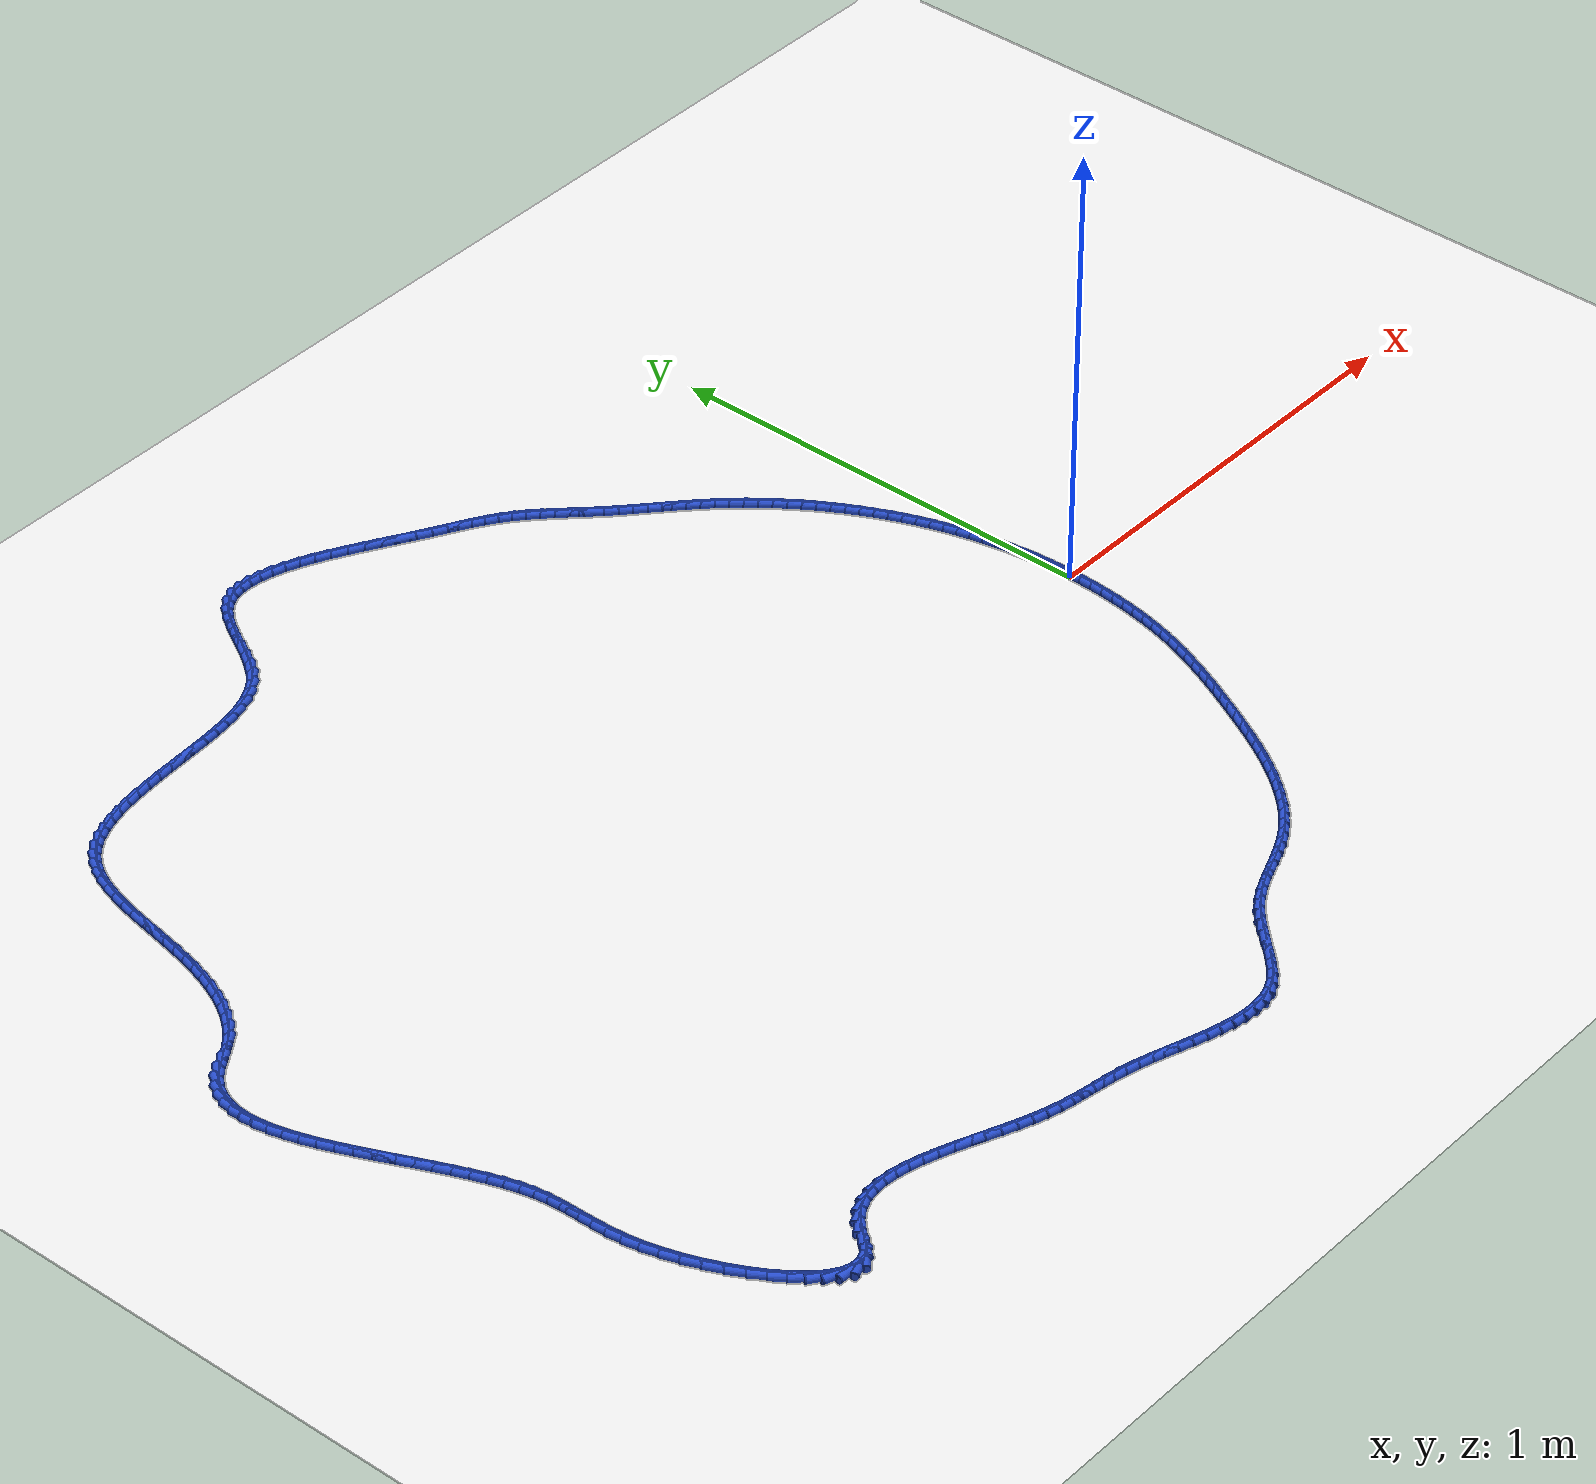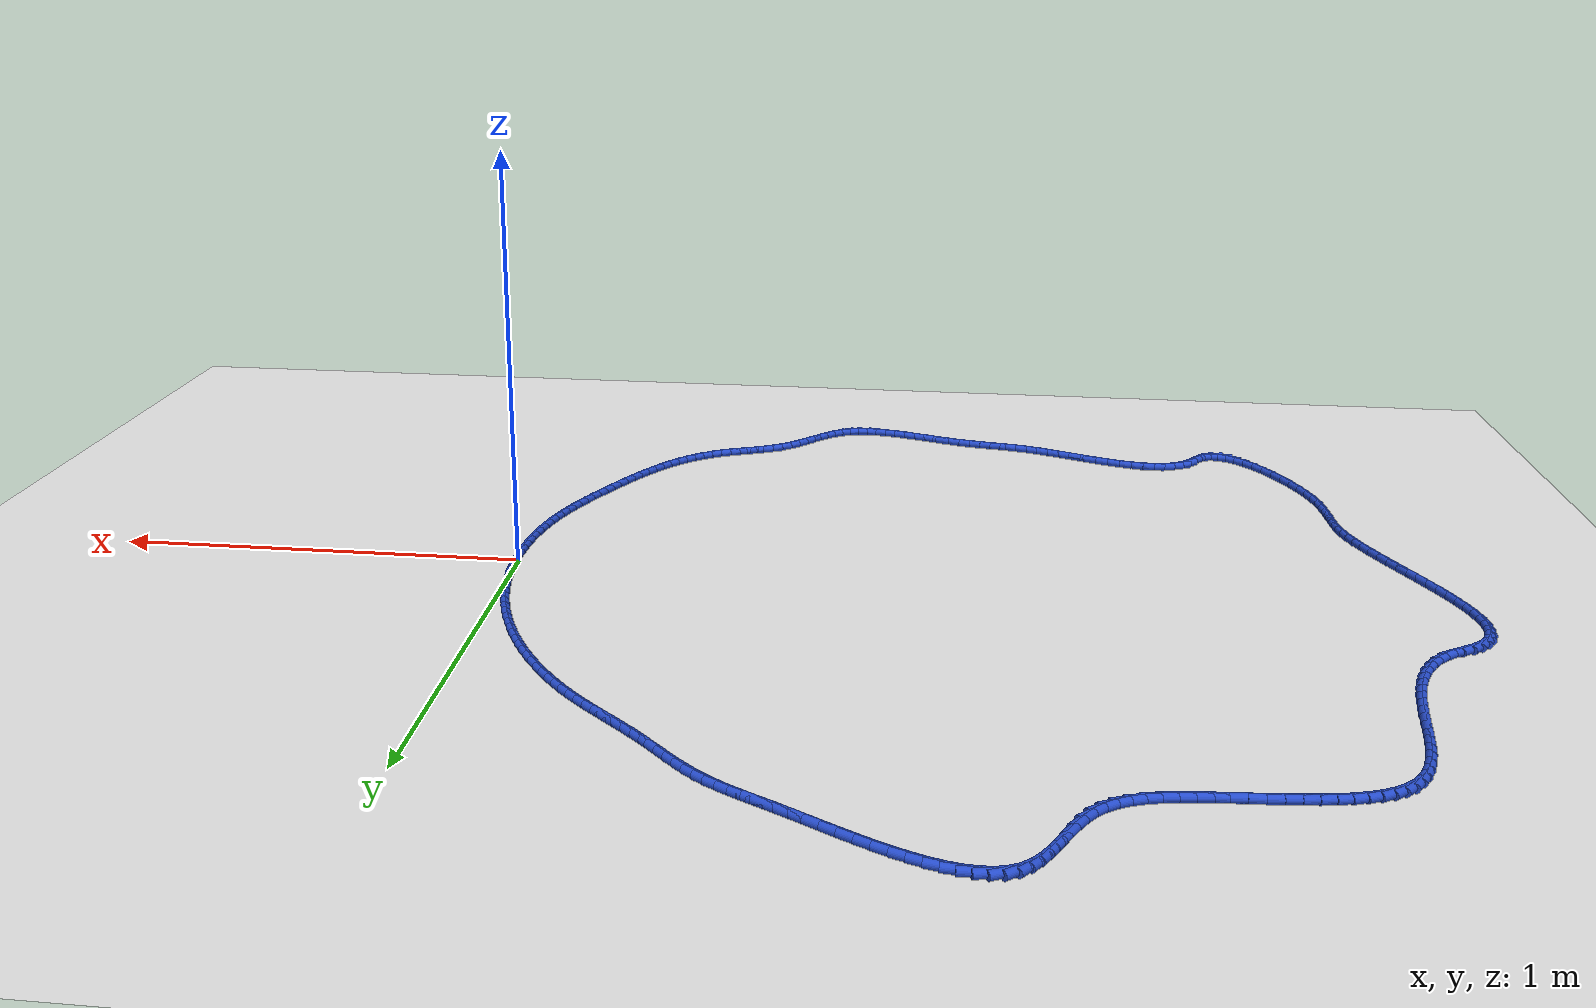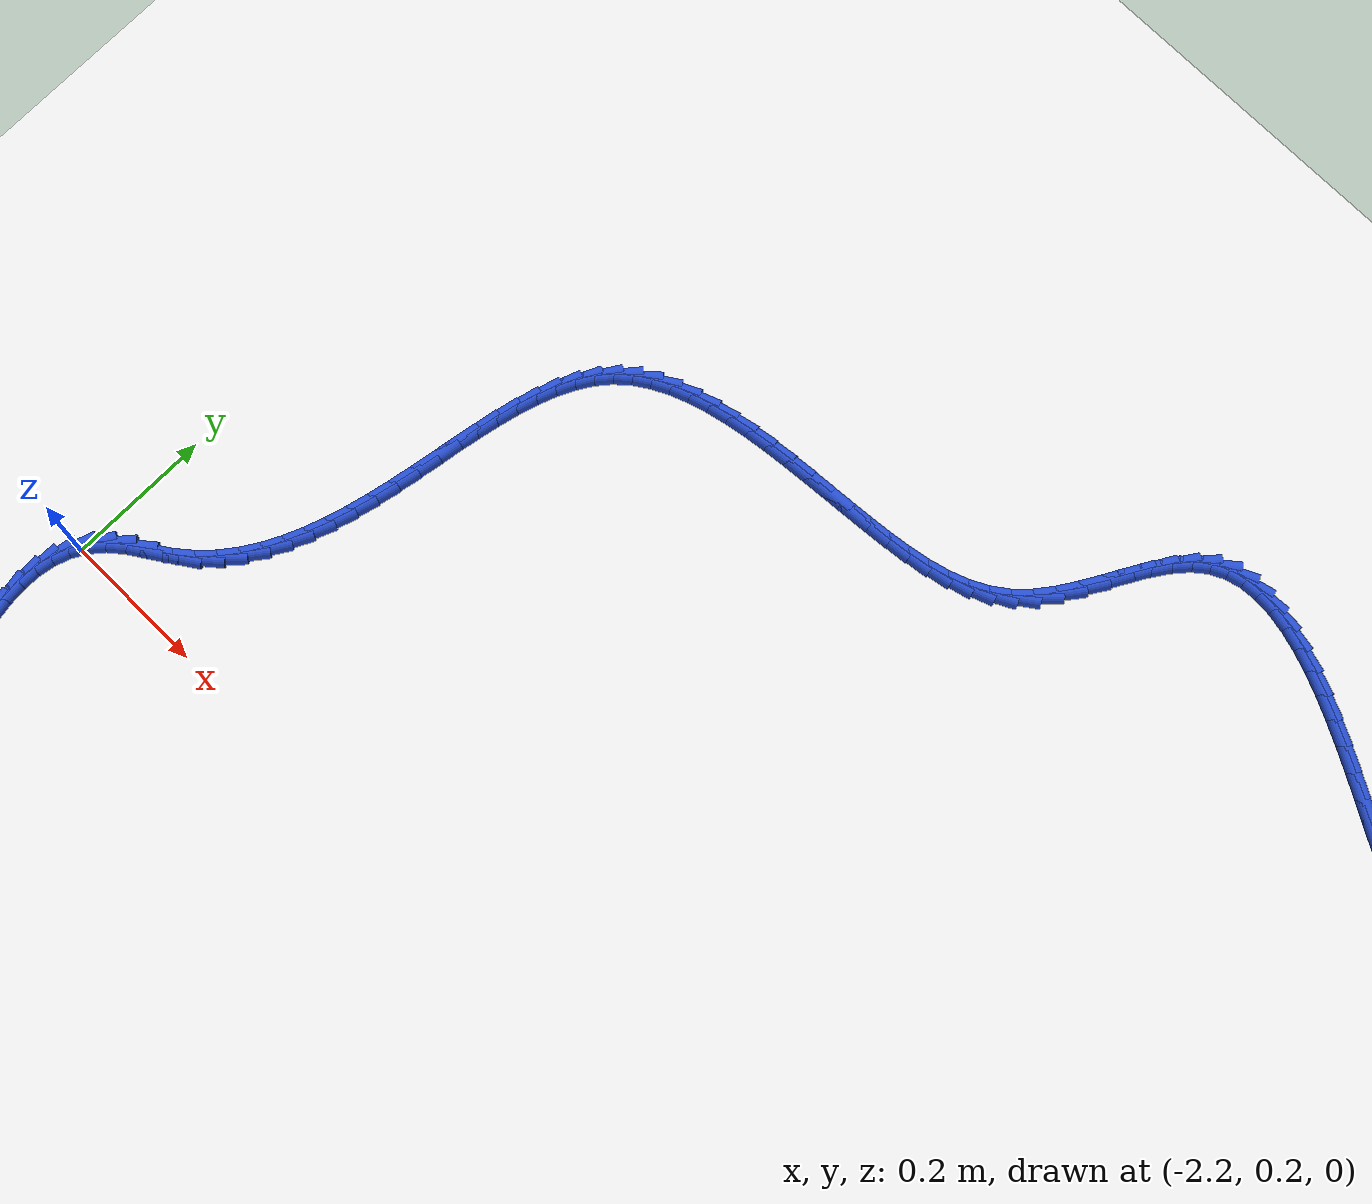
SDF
<sdf version="1.6">
 <world name="default">
  <light name="sun" type="directional">
   <pose>0 0 10 0 -0 0</pose>
   <diffuse>0.8 0.8 0.8 1</diffuse>
   <specular>0.2 0.2 0.2 1</specular>
   <attenuation>
    <range>1000</range>
    <constant>0.9</constant>
    <linear>0.01</linear>
    <quadratic>0.001</quadratic>
   </attenuation>
   <direction>-0.5 0.1 -0.9</direction>
  </light>
  <model name="ground_plane">
   <static>1</static>
   <link name="link">
    <collision name="collision">
     <geometry><plane><normal>0 0 1</normal><size>100 100</size></plane></geometry>
     <surface><friction><ode><mu>100</mu><mu2>50</mu2></ode></friction></surface>
    </collision>
    <visual name="visual">
     <cast_shadows>0</cast_shadows>
     <geometry><plane><normal>0 0 1</normal><size>100 100</size></plane></geometry>
     <material>
      <script><uri>file://media/materials/scripts/gazebo.material</uri><name>Gazebo/WhiteGlow</name></script>
     </material>
    </visual>
   </link>
  </model>
  <gravity>0 0 -9.8</gravity>
  <magnetic_field>6e-06 2.3e-05 -4.2e-05</magnetic_field>
  <atmosphere type="adiabatic"/>
  <physics name="default_physics" default="0" type="ode">
   <max_step_size>0.001</max_step_size>
   <real_time_factor>1</real_time_factor>
   <real_time_update_rate>1000</real_time_update_rate>
  </physics>
  <scene><ambient>0.4 0.4 0.4 1</ambient><background>0.7 0.7 0.7 1</background><shadows>1</shadows></scene>
  <spherical_coordinates>
   <surface_model>EARTH_WGS84</surface_model>
   <latitude_deg>0</latitude_deg>
   <longitude_deg>0</longitude_deg>
   <elevation>0</elevation>
   <heading_deg>0</heading_deg>
  </spherical_coordinates>
  <model name="line">
   <link name="link_0">
    <pose>1.0408340855860843e-17 -8.326672684688674e-17 0.01 0 1.57 -1.5555609442046128</pose>
    <collision name="collision">
     <geometry><cylinder><radius>0.01</radius><length>0.08</length></cylinder></geometry>
    </collision>
    <visual name="visual">
     <material>
      <script><name>Gazebo/Blue</name><uri>file://media/materials/scripts/gazebo.material</uri></script>
     </material>
     <geometry><cylinder><radius>0.01</radius><length>0.08</length></cylinder></geometry>
    </visual>
   </link>
   <link name="link_1">
    <pose>-0.0004483978259181032 0.02942906941494574 0.01 0 1.57 -1.5272894492918065</pose>
    <collision name="collision">
     <geometry><cylinder><radius>0.01</radius><length>0.08</length></cylinder></geometry>
    </collision>
    <visual name="visual">
     <material>
      <script><name>Gazebo/Blue</name><uri>file://media/materials/scripts/gazebo.material</uri></script>
     </material>
     <geometry><cylinder><radius>0.01</radius><length>0.08</length></cylinder></geometry>
    </visual>
   </link>
   <link name="link_2">
    <pose>-0.0017266899508206668 0.05879190946905788 0.01 0 1.57 -1.4985885119974234</pose>
    <collision name="collision">
     <geometry><cylinder><radius>0.01</radius><length>0.08</length></cylinder></geometry>
    </collision>
    <visual name="visual">
     <material>
      <script><name>Gazebo/Blue</name><uri>file://media/materials/scripts/gazebo.material</uri></script>
     </material>
     <geometry><cylinder><radius>0.01</radius><length>0.08</length></cylinder></geometry>
    </visual>
   </link>
   <link name="link_3">
    <pose>-0.0038447721193070224 0.08807405420118282 0.01 0 1.57 -1.4694633829766284</pose>
    <collision name="collision">
     <geometry><cylinder><radius>0.01</radius><length>0.08</length></cylinder></geometry>
    </collision>
    <visual name="visual">
     <material>
      <script><name>Gazebo/Blue</name><uri>file://media/materials/scripts/gazebo.material</uri></script>
     </material>
     <geometry><cylinder><radius>0.01</radius><length>0.08</length></cylinder></geometry>
    </visual>
   </link>
   <link name="link_4">
    <pose>-0.006812540075976516 0.11726103765016704 0.01 0 1.57 -1.4399222260830222</pose>
    <collision name="collision">
     <geometry><cylinder><radius>0.01</radius><length>0.08</length></cylinder></geometry>
    </collision>
    <visual name="visual">
     <material>
      <script><name>Gazebo/Blue</name><uri>file://media/materials/scripts/gazebo.material</uri></script>
     </material>
     <geometry><cylinder><radius>0.01</radius><length>0.08</length></cylinder></geometry>
    </visual>
   </link>
   <link name="link_5">
    <pose>-0.010639889565428492 0.146338393854857 0.01 0 1.57 -1.409976273621533</pose>
    <collision name="collision">
     <geometry><cylinder><radius>0.01</radius><length>0.08</length></cylinder></geometry>
    </collision>
    <visual name="visual">
     <material>
      <script><name>Gazebo/Blue</name><uri>file://media/materials/scripts/gazebo.material</uri></script>
     </material>
     <geometry><cylinder><radius>0.01</radius><length>0.08</length></cylinder></geometry>
    </visual>
   </link>
   <link name="link_6">
    <pose>-0.015336716332262306 0.1752916568540992 0.01 0 1.57 -1.3796399552273813</pose>
    <collision name="collision">
     <geometry><cylinder><radius>0.01</radius><length>0.08</length></cylinder></geometry>
    </collision>
    <visual name="visual">
     <material>
      <script><name>Gazebo/Blue</name><uri>file://media/materials/scripts/gazebo.material</uri></script>
     </material>
     <geometry><cylinder><radius>0.01</radius><length>0.08</length></cylinder></geometry>
    </visual>
   </link>
   <link name="link_7">
    <pose>-0.020912916121077284 0.20410636068674004 0.01 0 1.57 -1.348930993899488</pose>
    <collision name="collision">
     <geometry><cylinder><radius>0.01</radius><length>0.08</length></cylinder></geometry>
    </collision>
    <visual name="visual">
     <material>
      <script><name>Gazebo/Blue</name><uri>file://media/materials/scripts/gazebo.material</uri></script>
     </material>
     <geometry><cylinder><radius>0.01</radius><length>0.08</length></cylinder></geometry>
    </visual>
   </link>
   <link name="link_8">
    <pose>-0.027378384676472786 0.23276803939162607 0.01 0 1.57 -1.3178705495063912</pose>
    <collision name="collision">
     <geometry><cylinder><radius>0.01</radius><length>0.08</length></cylinder></geometry>
    </collision>
    <visual name="visual">
     <material>
      <script><name>Gazebo/Blue</name><uri>file://media/materials/scripts/gazebo.material</uri></script>
     </material>
     <geometry><cylinder><radius>0.01</radius><length>0.08</length></cylinder></geometry>
    </visual>
   </link>
   <link name="link_9">
    <pose>-0.03474301466962922 0.2612622253136308 0.01 0 1.57 -1.286651770982013</pose>
    <collision name="collision">
     <geometry><cylinder><radius>0.01</radius><length>0.08</length></cylinder></geometry>
    </collision>
    <visual name="visual">
     <material>
      <script><name>Gazebo/Blue</name><uri>file://media/materials/scripts/gazebo.material</uri></script>
     </material>
     <geometry><cylinder><radius>0.01</radius><length>0.08</length></cylinder></geometry>
    </visual>
   </link>
   <link name="link_10">
    <pose>-0.04301051952280737 0.2895710449877822 0.01 0 1.57 -1.2557895713142748</pose>
    <collision name="collision">
     <geometry><cylinder><radius>0.01</radius><length>0.08</length></cylinder></geometry>
    </collision>
    <visual name="visual">
     <material>
      <script><name>Gazebo/Blue</name><uri>file://media/materials/scripts/gazebo.material</uri></script>
     </material>
     <geometry><cylinder><radius>0.01</radius><length>0.08</length></cylinder></geometry>
    </visual>
   </link>
   <link name="link_11">
    <pose>-0.05216548107256712 0.3176660802140142 0.01 0 1.57 -1.2253354255580937</pose>
    <collision name="collision">
     <geometry><cylinder><radius>0.01</radius><length>0.08</length></cylinder></geometry>
    </collision>
    <visual name="visual">
     <material>
      <script><name>Gazebo/Blue</name><uri>file://media/materials/scripts/gazebo.material</uri></script>
     </material>
     <geometry><cylinder><radius>0.01</radius><length>0.08</length></cylinder></geometry>
    </visual>
   </link>
   <link name="link_12">
    <pose>-0.062188789829416995 0.3455168782481318 0.01 0 1.57 -1.1952357554981379</pose>
    <collision name="collision">
     <geometry><cylinder><radius>0.01</radius><length>0.08</length></cylinder></geometry>
    </collision>
    <visual name="visual">
     <material>
      <script><name>Gazebo/Blue</name><uri>file://media/materials/scripts/gazebo.material</uri></script>
     </material>
     <geometry><cylinder><radius>0.01</radius><length>0.08</length></cylinder></geometry>
    </visual>
   </link>
   <link name="link_13">
    <pose>-0.07306133630386541 0.37309298634594 0.01 0 1.57 -1.1654362908679599</pose>
    <collision name="collision">
     <geometry><cylinder><radius>0.01</radius><length>0.08</length></cylinder></geometry>
    </collision>
    <visual name="visual">
     <material>
      <script><name>Gazebo/Blue</name><uri>file://media/materials/scripts/gazebo.material</uri></script>
     </material>
     <geometry><cylinder><radius>0.01</radius><length>0.08</length></cylinder></geometry>
    </visual>
   </link>
   <link name="link_14">
    <pose>-0.08476401100642092 0.400363951763244 0.01 0 1.57 -1.1358822310072698</pose>
    <collision name="collision">
     <geometry><cylinder><radius>0.01</radius><length>0.08</length></cylinder></geometry>
    </collision>
    <visual name="visual">
     <material>
      <script><name>Gazebo/Blue</name><uri>file://media/materials/scripts/gazebo.material</uri></script>
     </material>
     <geometry><cylinder><radius>0.01</radius><length>0.08</length></cylinder></geometry>
    </visual>
   </link>
   <link name="link_15">
    <pose>-0.09727770444759203 0.42729932175584906 0.01 0 1.57 -1.1065183614631748</pose>
    <collision name="collision">
     <geometry><cylinder><radius>0.01</radius><length>0.08</length></cylinder></geometry>
    </collision>
    <visual name="visual">
     <material>
      <script><name>Gazebo/Blue</name><uri>file://media/materials/scripts/gazebo.material</uri></script>
     </material>
     <geometry><cylinder><radius>0.01</radius><length>0.08</length></cylinder></geometry>
    </visual>
   </link>
   <link name="link_16">
    <pose>-0.1105833071378872 0.45386864357956 0.01 0 1.57 -1.0772891339735309</pose>
    <collision name="collision">
     <geometry><cylinder><radius>0.01</radius><length>0.08</length></cylinder></geometry>
    </collision>
    <visual name="visual">
     <material>
      <script><name>Gazebo/Blue</name><uri>file://media/materials/scripts/gazebo.material</uri></script>
     </material>
     <geometry><cylinder><radius>0.01</radius><length>0.08</length></cylinder></geometry>
    </visual>
   </link>
   <link name="link_17">
    <pose>-0.12466170958781495 0.4800414644901822 0.01 0 1.57 -1.0481387179529276</pose>
    <collision name="collision">
     <geometry><cylinder><radius>0.01</radius><length>0.08</length></cylinder></geometry>
    </collision>
    <visual name="visual">
     <material>
      <script><name>Gazebo/Blue</name><uri>file://media/materials/scripts/gazebo.material</uri></script>
     </material>
     <geometry><cylinder><radius>0.01</radius><length>0.08</length></cylinder></geometry>
    </visual>
   </link>
   <link name="link_18">
    <pose>-0.13949380230788375 0.5057873317435205 0.01 0 1.57 -1.019011031316761</pose>
    <collision name="collision">
     <geometry><cylinder><radius>0.01</radius><length>0.08</length></cylinder></geometry>
    </collision>
    <visual name="visual">
     <material>
      <script><name>Gazebo/Blue</name><uri>file://media/materials/scripts/gazebo.material</uri></script>
     </material>
     <geometry><cylinder><radius>0.01</radius><length>0.08</length></cylinder></geometry>
    </visual>
   </link>
   <link name="link_19">
    <pose>-0.15506047580860213 0.5310757925953802 0.01 0 1.57 -0.989849758271775</pose>
    <collision name="collision">
     <geometry><cylinder><radius>0.01</radius><length>0.08</length></cylinder></geometry>
    </collision>
    <visual name="visual">
     <material>
      <script><name>Gazebo/Blue</name><uri>file://media/materials/scripts/gazebo.material</uri></script>
     </material>
     <geometry><cylinder><radius>0.01</radius><length>0.08</length></cylinder></geometry>
    </visual>
   </link>
   <link name="link_20">
    <pose>-0.17134262060047864 0.5558763943015665 0.01 0 1.57 -0.9605983616050993</pose>
    <collision name="collision">
     <geometry><cylinder><radius>0.01</radius><length>0.08</length></cylinder></geometry>
    </collision>
    <visual name="visual">
     <material>
      <script><name>Gazebo/Blue</name><uri>file://media/materials/scripts/gazebo.material</uri></script>
     </material>
     <geometry><cylinder><radius>0.01</radius><length>0.08</length></cylinder></geometry>
    </visual>
   </link>
   <link name="link_21">
    <pose>-0.18832112719402166 0.5801586841178844 0.01 0 1.57 -0.9312000970392649</pose>
    <collision name="collision">
     <geometry><cylinder><radius>0.01</radius><length>0.08</length></cylinder></geometry>
    </collision>
    <visual name="visual">
     <material>
      <script><name>Gazebo/Blue</name><uri>file://media/materials/scripts/gazebo.material</uri></script>
     </material>
     <geometry><cylinder><radius>0.01</radius><length>0.08</length></cylinder></geometry>
    </visual>
   </link>
   <link name="link_22">
    <pose>-0.20597688609973971 0.6038922093001388 0.01 0 1.57 -0.9015980373990731</pose>
    <collision name="collision">
     <geometry><cylinder><radius>0.01</radius><length>0.08</length></cylinder></geometry>
    </collision>
    <visual name="visual">
     <material>
      <script><name>Gazebo/Blue</name><uri>file://media/materials/scripts/gazebo.material</uri></script>
     </material>
     <geometry><cylinder><radius>0.01</radius><length>0.08</length></cylinder></geometry>
    </visual>
   </link>
   <link name="link_23">
    <pose>-0.22429078782814138 0.6270465171041351 0.01 0 1.57 -0.8717351146596326</pose>
    <collision name="collision">
     <geometry><cylinder><radius>0.01</radius><length>0.08</length></cylinder></geometry>
    </collision>
    <visual name="visual">
     <material>
      <script><name>Gazebo/Blue</name><uri>file://media/materials/scripts/gazebo.material</uri></script>
     </material>
     <geometry><cylinder><radius>0.01</radius><length>0.08</length></cylinder></geometry>
    </visual>
   </link>
   <link name="link_24">
    <pose>-0.24324372288973511 0.6495911547856783 0.01 0 1.57 -0.8415541884047403</pose>
    <collision name="collision">
     <geometry><cylinder><radius>0.01</radius><length>0.08</length></cylinder></geometry>
    </collision>
    <visual name="visual">
     <material>
      <script><name>Gazebo/Blue</name><uri>file://media/materials/scripts/gazebo.material</uri></script>
     </material>
     <geometry><cylinder><radius>0.01</radius><length>0.08</length></cylinder></geometry>
    </visual>
   </link>
   <link name="link_25">
    <pose>-0.26281658179502937 0.6714956696005736 0.01 0 1.57 -0.8110014844351243</pose>
    <collision name="collision">
     <geometry><cylinder><radius>0.01</radius><length>0.08</length></cylinder></geometry>
    </collision>
    <visual name="visual">
     <material>
      <script><name>Gazebo/Blue</name><uri>file://media/materials/scripts/gazebo.material</uri></script>
     </material>
     <geometry><cylinder><radius>0.01</radius><length>0.08</length></cylinder></geometry>
    </visual>
   </link>
   <link name="link_26">
    <pose>-0.2829902071569155 0.6927297001905018 0.01 0 1.57 -0.7818047484688971</pose>
    <collision name="collision">
     <geometry><cylinder><radius>0.01</radius><length>0.08</length></cylinder></geometry>
    </collision>
    <visual name="visual">
     <material>
      <script><name>Gazebo/Blue</name><uri>file://media/materials/scripts/gazebo.material</uri></script>
     </material>
     <geometry><cylinder><radius>0.01</radius><length>0.08</length></cylinder></geometry>
    </visual>
   </link>
   <link name="link_27">
    <pose>-0.3037201316658635 0.7133111750612405 0.01 0 1.57 -0.7587226585505692</pose>
    <collision name="collision">
     <geometry><cylinder><radius>0.01</radius><length>0.08</length></cylinder></geometry>
    </collision>
    <visual name="visual">
     <material>
      <script><name>Gazebo/Blue</name><uri>file://media/materials/scripts/gazebo.material</uri></script>
     </material>
     <geometry><cylinder><radius>0.01</radius><length>0.08</length></cylinder></geometry>
    </visual>
   </link>
   <link name="link_28">
    <pose>-0.3248950701400707 0.7333855073436736 0.01 0 1.57 -0.7426320465863961</pose>
    <collision name="collision">
     <geometry><cylinder><radius>0.01</radius><length>0.08</length></cylinder></geometry>
    </collision>
    <visual name="visual">
     <material>
      <script><name>Gazebo/Blue</name><uri>file://media/materials/scripts/gazebo.material</uri></script>
     </material>
     <geometry><cylinder><radius>0.01</radius><length>0.08</length></cylinder></geometry>
    </visual>
   </link>
   <link name="link_29">
    <pose>-0.3463928390266051 0.7531189036287337 0.01 0 1.57 -0.7335807956889542</pose>
    <collision name="collision">
     <geometry><cylinder><radius>0.01</radius><length>0.08</length></cylinder></geometry>
    </collision>
    <visual name="visual">
     <material>
      <script><name>Gazebo/Blue</name><uri>file://media/materials/scripts/gazebo.material</uri></script>
     </material>
     <geometry><cylinder><radius>0.01</radius><length>0.08</length></cylinder></geometry>
    </visual>
   </link>
   <link name="link_30">
    <pose>-0.3680912547725344 0.7726775705073525 0.01 0 1.57 -0.7315693675636631</pose>
    <collision name="collision">
     <geometry><cylinder><radius>0.01</radius><length>0.08</length></cylinder></geometry>
    </collision>
    <visual name="visual">
     <material>
      <script><name>Gazebo/Blue</name><uri>file://media/materials/scripts/gazebo.material</uri></script>
     </material>
     <geometry><cylinder><radius>0.01</radius><length>0.08</length></cylinder></geometry>
    </visual>
   </link>
   <link name="link_31">
    <pose>-0.3898681338249267 0.7922277145704631 0.01 0 1.57 -0.7365643659230418</pose>
    <collision name="collision">
     <geometry><cylinder><radius>0.01</radius><length>0.08</length></cylinder></geometry>
    </collision>
    <visual name="visual">
     <material>
      <script><name>Gazebo/Blue</name><uri>file://media/materials/scripts/gazebo.material</uri></script>
     </material>
     <geometry><cylinder><radius>0.01</radius><length>0.08</length></cylinder></geometry>
    </visual>
   </link>
   <link name="link_32">
    <pose>-0.4116012926308501 0.8119355424089982 0.01 0 1.57 -0.7485020615696558</pose>
    <collision name="collision">
     <geometry><cylinder><radius>0.01</radius><length>0.08</length></cylinder></geometry>
    </collision>
    <visual name="visual">
     <material>
      <script><name>Gazebo/Blue</name><uri>file://media/materials/scripts/gazebo.material</uri></script>
     </material>
     <geometry><cylinder><radius>0.01</radius><length>0.08</length></cylinder></geometry>
    </visual>
   </link>
   <link name="link_33">
    <pose>-0.4331685476373724 0.83196726061389 0.01 0 1.57 -0.7672642424907525</pose>
    <collision name="collision">
     <geometry><cylinder><radius>0.01</radius><length>0.08</length></cylinder></geometry>
    </collision>
    <visual name="visual">
     <material>
      <script><name>Gazebo/Blue</name><uri>file://media/materials/scripts/gazebo.material</uri></script>
     </material>
     <geometry><cylinder><radius>0.01</radius><length>0.08</length></cylinder></geometry>
    </visual>
   </link>
   <link name="link_34">
    <pose>-0.45444798522687163 0.8524886030653619 0.01 0 1.57 -0.7873415162183817</pose>
    <collision name="collision">
     <geometry><cylinder><radius>0.01</radius><length>0.08</length></cylinder></geometry>
    </collision>
    <visual name="visual">
     <material>
      <script><name>Gazebo/Blue</name><uri>file://media/materials/scripts/gazebo.material</uri></script>
     </material>
     <geometry><cylinder><radius>0.01</radius><length>0.08</length></cylinder></geometry>
    </visual>
   </link>
   <link name="link_35">
    <pose>-0.47539962058452784 0.8735218299261602 0.01 0 1.57 -0.7959267499839467</pose>
    <collision name="collision">
     <geometry><cylinder><radius>0.01</radius><length>0.08</length></cylinder></geometry>
    </collision>
    <visual name="visual">
     <material>
      <script><name>Gazebo/Blue</name><uri>file://media/materials/scripts/gazebo.material</uri></script>
     </material>
     <geometry><cylinder><radius>0.01</radius><length>0.08</length></cylinder></geometry>
    </visual>
   </link>
   <link name="link_36">
    <pose>-0.4961802085169701 0.8947446709387192 0.01 0 1.57 -0.7912380117444903</pose>
    <collision name="collision">
     <geometry><cylinder><radius>0.01</radius><length>0.08</length></cylinder></geometry>
    </collision>
    <visual name="visual">
     <material>
      <script><name>Gazebo/Blue</name><uri>file://media/materials/scripts/gazebo.material</uri></script>
     </material>
     <geometry><cylinder><radius>0.01</radius><length>0.08</length></cylinder></geometry>
    </visual>
   </link>
   <link name="link_37">
    <pose>-0.5169754287399421 0.9157842025453363 0.01 0 1.57 -0.7730495137718516</pose>
    <collision name="collision">
     <geometry><cylinder><radius>0.01</radius><length>0.08</length></cylinder></geometry>
    </collision>
    <visual name="visual">
     <material>
      <script><name>Gazebo/Blue</name><uri>file://media/materials/scripts/gazebo.material</uri></script>
     </material>
     <geometry><cylinder><radius>0.01</radius><length>0.08</length></cylinder></geometry>
    </visual>
   </link>
   <link name="link_38">
    <pose>-0.5379709609691868 0.9362675011883084 0.01 0 1.57 -0.7407874458995741</pose>
    <collision name="collision">
     <geometry><cylinder><radius>0.01</radius><length>0.08</length></cylinder></geometry>
    </collision>
    <visual name="visual">
     <material>
      <script><name>Gazebo/Blue</name><uri>file://media/materials/scripts/gazebo.material</uri></script>
     </material>
     <geometry><cylinder><radius>0.01</radius><length>0.08</length></cylinder></geometry>
    </visual>
   </link>
   <link name="link_39">
    <pose>-0.5593524849204481 0.9558216433099324 0.01 0 1.57 -0.6936009312830728</pose>
    <collision name="collision">
     <geometry><cylinder><radius>0.01</radius><length>0.08</length></cylinder></geometry>
    </collision>
    <visual name="visual">
     <material>
      <script><name>Gazebo/Blue</name><uri>file://media/materials/scripts/gazebo.material</uri></script>
     </material>
     <geometry><cylinder><radius>0.01</radius><length>0.08</length></cylinder></geometry>
    </visual>
   </link>
   <link name="link_40">
    <pose>-0.5813056803094686 0.9740737053525046 0.01 0 1.57 -0.6342538687774706</pose>
    <collision name="collision">
     <geometry><cylinder><radius>0.01</radius><length>0.08</length></cylinder></geometry>
    </collision>
    <visual name="visual">
     <material>
      <script><name>Gazebo/Blue</name><uri>file://media/materials/scripts/gazebo.material</uri></script>
     </material>
     <geometry><cylinder><radius>0.01</radius><length>0.08</length></cylinder></geometry>
    </visual>
   </link>
   <link name="link_41">
    <pose>-0.6039971105438559 0.9907666628071685 0.01 0 1.57 -0.5806487105859068</pose>
    <collision name="collision">
     <geometry><cylinder><radius>0.01</radius><length>0.08</length></cylinder></geometry>
    </collision>
    <visual name="visual">
     <material>
      <script><name>Gazebo/Blue</name><uri>file://media/materials/scripts/gazebo.material</uri></script>
     </material>
     <geometry><cylinder><radius>0.01</radius><length>0.08</length></cylinder></geometry>
    </visual>
   </link>
   <link name="link_42">
    <pose>-0.62750336000404 1.0061890192864564 0.01 0 1.57 -0.5397523954169569</pose>
    <collision name="collision">
     <geometry><cylinder><radius>0.01</radius><length>0.08</length></cylinder></geometry>
    </collision>
    <visual name="visual">
     <material>
      <script><name>Gazebo/Blue</name><uri>file://media/materials/scripts/gazebo.material</uri></script>
     </material>
     <geometry><cylinder><radius>0.01</radius><length>0.08</length></cylinder></geometry>
    </visual>
   </link>
   <link name="link_43">
    <pose>-0.6518745633011798 1.0207896390268765 0.01 0 1.57 -0.5125165849322124</pose>
    <collision name="collision">
     <geometry><cylinder><radius>0.01</radius><length>0.08</length></cylinder></geometry>
    </collision>
    <visual name="visual">
     <material>
      <script><name>Gazebo/Blue</name><uri>file://media/materials/scripts/gazebo.material</uri></script>
     </material>
     <geometry><cylinder><radius>0.01</radius><length>0.08</length></cylinder></geometry>
    </visual>
   </link>
   <link name="link_44">
    <pose>-0.6771608514583765 1.0350174080187409 0.01 0 1.57 -0.49890042588356615</pose>
    <collision name="collision">
     <geometry><cylinder><radius>0.01</radius><length>0.08</length></cylinder></geometry>
    </collision>
    <visual name="visual">
     <material>
      <script><name>Gazebo/Blue</name><uri>file://media/materials/scripts/gazebo.material</uri></script>
     </material>
     <geometry><cylinder><radius>0.01</radius><length>0.08</length></cylinder></geometry>
    </visual>
   </link>
   <link name="link_45">
    <pose>-0.703412355498731 1.0493212122523616 0.01 0 1.57 -0.4980993169900236</pose>
    <collision name="collision">
     <geometry><cylinder><radius>0.01</radius><length>0.08</length></cylinder></geometry>
    </collision>
    <visual name="visual">
     <material>
      <script><name>Gazebo/Blue</name><uri>file://media/materials/scripts/gazebo.material</uri></script>
     </material>
     <geometry><cylinder><radius>0.01</radius><length>0.08</length></cylinder></geometry>
    </visual>
   </link>
   <link name="link_46">
    <pose>-0.7306792064453443 1.0641499377180512 0.01 0 1.57 -0.5082319572374002</pose>
    <collision name="collision">
     <geometry><cylinder><radius>0.01</radius><length>0.08</length></cylinder></geometry>
    </collision>
    <visual name="visual">
     <material>
      <script><name>Gazebo/Blue</name><uri>file://media/materials/scripts/gazebo.material</uri></script>
     </material>
     <geometry><cylinder><radius>0.01</radius><length>0.08</length></cylinder></geometry>
    </visual>
   </link>
   <link name="link_47">
    <pose>-0.7590039103705701 1.0799279244129343 0.01 0 1.57 -0.5183036198236411</pose>
    <collision name="collision">
     <geometry><cylinder><radius>0.01</radius><length>0.08</length></cylinder></geometry>
    </collision>
    <visual name="visual">
     <material>
      <script><name>Gazebo/Blue</name><uri>file://media/materials/scripts/gazebo.material</uri></script>
     </material>
     <geometry><cylinder><radius>0.01</radius><length>0.08</length></cylinder></geometry>
    </visual>
   </link>
   <link name="link_48">
    <pose>-0.7882892391720583 1.0966296846285235 0.01 0 1.57 -0.5203530635979943</pose>
    <collision name="collision">
     <geometry><cylinder><radius>0.01</radius><length>0.08</length></cylinder></geometry>
    </collision>
    <visual name="visual">
     <material>
      <script><name>Gazebo/Blue</name><uri>file://media/materials/scripts/gazebo.material</uri></script>
     </material>
     <geometry><cylinder><radius>0.01</radius><length>0.08</length></cylinder></geometry>
    </visual>
   </link>
   <link name="link_49">
    <pose>-0.8183155599874655 1.1138356892383254 0.01 0 1.57 -0.5147900094374656</pose>
    <collision name="collision">
     <geometry><cylinder><radius>0.01</radius><length>0.08</length></cylinder></geometry>
    </collision>
    <visual name="visual">
     <material>
      <script><name>Gazebo/Blue</name><uri>file://media/materials/scripts/gazebo.material</uri></script>
     </material>
     <geometry><cylinder><radius>0.01</radius><length>0.08</length></cylinder></geometry>
    </visual>
   </link>
   <link name="link_50">
    <pose>-0.8488590999459876 1.1311130817354016 0.01 0 1.57 -0.5017366412286963</pose>
    <collision name="collision">
     <geometry><cylinder><radius>0.01</radius><length>0.08</length></cylinder></geometry>
    </collision>
    <visual name="visual">
     <material>
      <script><name>Gazebo/Blue</name><uri>file://media/materials/scripts/gazebo.material</uri></script>
     </material>
     <geometry><cylinder><radius>0.01</radius><length>0.08</length></cylinder></geometry>
    </visual>
   </link>
   <link name="link_51">
    <pose>-0.87969608617682 1.1480290056128148 0.01 0 1.57 -0.48079533815945563</pose>
    <collision name="collision">
     <geometry><cylinder><radius>0.01</radius><length>0.08</length></cylinder></geometry>
    </collision>
    <visual name="visual">
     <material>
      <script><name>Gazebo/Blue</name><uri>file://media/materials/scripts/gazebo.material</uri></script>
     </material>
     <geometry><cylinder><radius>0.01</radius><length>0.08</length></cylinder></geometry>
    </visual>
   </link>
   <link name="link_52">
    <pose>-0.9106027458091585 1.1641506043636276 0.01 0 1.57 -0.45103398790445903</pose>
    <collision name="collision">
     <geometry><cylinder><radius>0.01</radius><length>0.08</length></cylinder></geometry>
    </collision>
    <visual name="visual">
     <material>
      <script><name>Gazebo/Blue</name><uri>file://media/materials/scripts/gazebo.material</uri></script>
     </material>
     <geometry><cylinder><radius>0.01</radius><length>0.08</length></cylinder></geometry>
    </visual>
   </link>
   <link name="link_53">
    <pose>-0.9413553059721987 1.179045021480902 0.01 0 1.57 -0.41090215143603803</pose>
    <collision name="collision">
     <geometry><cylinder><radius>0.01</radius><length>0.08</length></cylinder></geometry>
    </collision>
    <visual name="visual">
     <material>
      <script><name>Gazebo/Blue</name><uri>file://media/materials/scripts/gazebo.material</uri></script>
     </material>
     <geometry><cylinder><radius>0.01</radius><length>0.08</length></cylinder></geometry>
    </visual>
   </link>
   <link name="link_54">
    <pose>-0.9717299937951358 1.1922794004577 0.01 0 1.57 -0.35808124792651674</pose>
    <collision name="collision">
     <geometry><cylinder><radius>0.01</radius><length>0.08</length></cylinder></geometry>
    </collision>
    <visual name="visual">
     <material>
      <script><name>Gazebo/Blue</name><uri>file://media/materials/scripts/gazebo.material</uri></script>
     </material>
     <geometry><cylinder><radius>0.01</radius><length>0.08</length></cylinder></geometry>
    </visual>
   </link>
   <link name="link_55">
    <pose>-1.001503036407166 1.2034208847870846 0.01 0 1.57 -0.28928270697576575</pose>
    <collision name="collision">
     <geometry><cylinder><radius>0.01</radius><length>0.08</length></cylinder></geometry>
    </collision>
    <visual name="visual">
     <material>
      <script><name>Gazebo/Blue</name><uri>file://media/materials/scripts/gazebo.material</uri></script>
     </material>
     <geometry><cylinder><radius>0.01</radius><length>0.08</length></cylinder></geometry>
    </visual>
   </link>
   <link name="link_56">
    <pose>-1.0304506609374844 1.2120366179621174 0.01 0 1.57 -0.20006311036587493</pose>
    <collision name="collision">
     <geometry><cylinder><radius>0.01</radius><length>0.08</length></cylinder></geometry>
    </collision>
    <visual name="visual">
     <material>
      <script><name>Gazebo/Blue</name><uri>file://media/materials/scripts/gazebo.material</uri></script>
     </material>
     <geometry><cylinder><radius>0.01</radius><length>0.08</length></cylinder></geometry>
    </visual>
   </link>
   <link name="link_57">
    <pose>-1.0583490945152867 1.2176937434758608 0.01 0 1.57 -0.08488926168977587</pose>
    <collision name="collision">
     <geometry><cylinder><radius>0.01</radius><length>0.08</length></cylinder></geometry>
    </collision>
    <visual name="visual">
     <material>
      <script><name>Gazebo/Blue</name><uri>file://media/materials/scripts/gazebo.material</uri></script>
     </material>
     <geometry><cylinder><radius>0.01</radius><length>0.08</length></cylinder></geometry>
    </visual>
   </link>
   <link name="link_58">
    <pose>-1.0849745642697686 1.2199594048213767 0.01 0 1.57 0.06194761300042168</pose>
    <collision name="collision">
     <geometry><cylinder><radius>0.01</radius><length>0.08</length></cylinder></geometry>
    </collision>
    <visual name="visual">
     <material>
      <script><name>Gazebo/Blue</name><uri>file://media/materials/scripts/gazebo.material</uri></script>
     </material>
     <geometry><cylinder><radius>0.01</radius><length>0.08</length></cylinder></geometry>
    </visual>
   </link>
   <link name="link_59">
    <pose>-1.1101032973301257 1.2184007454917283 0.01 0 1.57 0.24352185874922996</pose>
    <collision name="collision">
     <geometry><cylinder><radius>0.01</radius><length>0.08</length></cylinder></geometry>
    </collision>
    <visual name="visual">
     <material>
      <script><name>Gazebo/Blue</name><uri>file://media/materials/scripts/gazebo.material</uri></script>
     </material>
     <geometry><cylinder><radius>0.01</radius><length>0.08</length></cylinder></geometry>
    </visual>
   </link>
   <link name="link_60">
    <pose>-1.1335115208255533 1.2125849089799772 0.01 0 1.57 0.45518498297352966</pose>
    <collision name="collision">
     <geometry><cylinder><radius>0.01</radius><length>0.08</length></cylinder></geometry>
    </collision>
    <visual name="visual">
     <material>
      <script><name>Gazebo/Blue</name><uri>file://media/materials/scripts/gazebo.material</uri></script>
     </material>
     <geometry><cylinder><radius>0.01</radius><length>0.08</length></cylinder></geometry>
    </visual>
   </link>
   <link name="link_61">
    <pose>-1.154975461885247 1.202079038779186 0.01 0 1.57 0.6783929036199875</pose>
    <collision name="collision">
     <geometry><cylinder><radius>0.01</radius><length>0.08</length></cylinder></geometry>
    </collision>
    <visual name="visual">
     <material>
      <script><name>Gazebo/Blue</name><uri>file://media/materials/scripts/gazebo.material</uri></script>
     </material>
     <geometry><cylinder><radius>0.01</radius><length>0.08</length></cylinder></geometry>
    </visual>
   </link>
   <link name="link_62">
    <pose>-1.174299023471863 1.1865041168821069 0.01 0 1.57 0.8586059670280725</pose>
    <collision name="collision">
     <geometry><cylinder><radius>0.01</radius><length>0.08</length></cylinder></geometry>
    </collision>
    <visual name="visual">
     <material>
      <script><name>Gazebo/Blue</name><uri>file://media/materials/scripts/gazebo.material</uri></script>
     </material>
     <geometry><cylinder><radius>0.01</radius><length>0.08</length></cylinder></geometry>
    </visual>
   </link>
   <link name="link_63">
    <pose>-1.1917201461635438 1.166325469646426 0.01 0 1.57 0.9729977720407559</pose>
    <collision name="collision">
     <geometry><cylinder><radius>0.01</radius><length>0.08</length></cylinder></geometry>
    </collision>
    <visual name="visual">
     <material>
      <script><name>Gazebo/Blue</name><uri>file://media/materials/scripts/gazebo.material</uri></script>
     </material>
     <geometry><cylinder><radius>0.01</radius><length>0.08</length></cylinder></geometry>
    </visual>
   </link>
   <link name="link_64">
    <pose>-1.20782138676357 1.1426788140996222 0.01 0 1.57 1.036142944541472</pose>
    <collision name="collision">
     <geometry><cylinder><radius>0.01</radius><length>0.08</length></cylinder></geometry>
    </collision>
    <visual name="visual">
     <material>
      <script><name>Gazebo/Blue</name><uri>file://media/materials/scripts/gazebo.material</uri></script>
     </material>
     <geometry><cylinder><radius>0.01</radius><length>0.08</length></cylinder></geometry>
    </visual>
   </link>
   <link name="link_65">
    <pose>-1.223194794719362 1.1167183335502058 0.01 0 1.57 1.058895613276001</pose>
    <collision name="collision">
     <geometry><cylinder><radius>0.01</radius><length>0.08</length></cylinder></geometry>
    </collision>
    <visual name="visual">
     <material>
      <script><name>Gazebo/Blue</name><uri>file://media/materials/scripts/gazebo.material</uri></script>
     </material>
     <geometry><cylinder><radius>0.01</radius><length>0.08</length></cylinder></geometry>
    </visual>
   </link>
   <link name="link_66">
    <pose>-1.2384324194783394 1.0895982113066878 0.01 0 1.57 1.0462875498071533</pose>
    <collision name="collision">
     <geometry><cylinder><radius>0.01</radius><length>0.08</length></cylinder></geometry>
    </collision>
    <visual name="visual">
     <material>
      <script><name>Gazebo/Blue</name><uri>file://media/materials/scripts/gazebo.material</uri></script>
     </material>
     <geometry><cylinder><radius>0.01</radius><length>0.08</length></cylinder></geometry>
    </visual>
   </link>
   <link name="link_67">
    <pose>-1.254126310487922 1.0624726306775802 0.01 0 1.57 0.9982939097079527</pose>
    <collision name="collision">
     <geometry><cylinder><radius>0.01</radius><length>0.08</length></cylinder></geometry>
    </collision>
    <visual name="visual">
     <material>
      <script><name>Gazebo/Blue</name><uri>file://media/materials/scripts/gazebo.material</uri></script>
     </material>
     <geometry><cylinder><radius>0.01</radius><length>0.08</length></cylinder></geometry>
    </visual>
   </link>
   <link name="link_68">
    <pose>-1.2708685171955292 1.036495774971394 0.01 0 1.57 0.910556349702019</pose>
    <collision name="collision">
     <geometry><cylinder><radius>0.01</radius><length>0.08</length></cylinder></geometry>
    </collision>
    <visual name="visual">
     <material>
      <script><name>Gazebo/Blue</name><uri>file://media/materials/scripts/gazebo.material</uri></script>
     </material>
     <geometry><cylinder><radius>0.01</radius><length>0.08</length></cylinder></geometry>
    </visual>
   </link>
   <link name="link_69">
    <pose>-1.2892510890485818 1.0128218274966403 0.01 0 1.57 0.776115957125846</pose>
    <collision name="collision">
     <geometry><cylinder><radius>0.01</radius><length>0.08</length></cylinder></geometry>
    </collision>
    <visual name="visual">
     <material>
      <script><name>Gazebo/Blue</name><uri>file://media/materials/scripts/gazebo.material</uri></script>
     </material>
     <geometry><cylinder><radius>0.01</radius><length>0.08</length></cylinder></geometry>
    </visual>
   </link>
   <link name="link_70">
    <pose>-1.3098594894146307 0.9925925022107727 0.01 0 1.57 0.614484283541485</pose>
    <collision name="collision">
     <geometry><cylinder><radius>0.01</radius><length>0.08</length></cylinder></geometry>
    </collision>
    <visual name="visual">
     <material>
      <script><name>Gazebo/Blue</name><uri>file://media/materials/scripts/gazebo.material</uri></script>
     </material>
     <geometry><cylinder><radius>0.01</radius><length>0.08</length></cylinder></geometry>
    </visual>
   </link>
   <link name="link_71">
    <pose>-1.3329396962462903 0.9763067691473565 0.01 0 1.57 0.46782374481326866</pose>
    <collision name="collision">
     <geometry><cylinder><radius>0.01</radius><length>0.08</length></cylinder></geometry>
    </collision>
    <visual name="visual">
     <material>
      <script><name>Gazebo/Blue</name><uri>file://media/materials/scripts/gazebo.material</uri></script>
     </material>
     <geometry><cylinder><radius>0.01</radius><length>0.08</length></cylinder></geometry>
    </visual>
   </link>
   <link name="link_72">
    <pose>-1.3582412241193096 0.963523649803511 0.01 0 1.57 0.3453031799460843</pose>
    <collision name="collision">
     <geometry><cylinder><radius>0.01</radius><length>0.08</length></cylinder></geometry>
    </collision>
    <visual name="visual">
     <material>
      <script><name>Gazebo/Blue</name><uri>file://media/materials/scripts/gazebo.material</uri></script>
     </material>
     <geometry><cylinder><radius>0.01</radius><length>0.08</length></cylinder></geometry>
    </visual>
   </link>
   <link name="link_73">
    <pose>-1.3854741772149084 0.9537275504189477 0.01 0 1.57 0.24843249446647223</pose>
    <collision name="collision">
     <geometry><cylinder><radius>0.01</radius><length>0.08</length></cylinder></geometry>
    </collision>
    <visual name="visual">
     <material>
      <script><name>Gazebo/Blue</name><uri>file://media/materials/scripts/gazebo.material</uri></script>
     </material>
     <geometry><cylinder><radius>0.01</radius><length>0.08</length></cylinder></geometry>
    </visual>
   </link>
   <link name="link_74">
    <pose>-1.4143486597143058 0.9464028772333779 0.01 0 1.57 0.17578917918295028</pose>
    <collision name="collision">
     <geometry><cylinder><radius>0.01</radius><length>0.08</length></cylinder></geometry>
    </collision>
    <visual name="visual">
     <material>
      <script><name>Gazebo/Blue</name><uri>file://media/materials/scripts/gazebo.material</uri></script>
     </material>
     <geometry><cylinder><radius>0.01</radius><length>0.08</length></cylinder></geometry>
    </visual>
   </link>
   <link name="link_75">
    <pose>-1.4445747757987222 0.9410340364865146 0.01 0 1.57 0.12490946053421849</pose>
    <collision name="collision">
     <geometry><cylinder><radius>0.01</radius><length>0.08</length></cylinder></geometry>
    </collision>
    <visual name="visual">
     <material>
      <script><name>Gazebo/Blue</name><uri>file://media/materials/scripts/gazebo.material</uri></script>
     </material>
     <geometry><cylinder><radius>0.01</radius><length>0.08</length></cylinder></geometry>
    </visual>
   </link>
   <link name="link_76">
    <pose>-1.4758626296493766 0.9371054344180683 0.01 0 1.57 0.09342088120840046</pose>
    <collision name="collision">
     <geometry><cylinder><radius>0.01</radius><length>0.08</length></cylinder></geometry>
    </collision>
    <visual name="visual">
     <material>
      <script><name>Gazebo/Blue</name><uri>file://media/materials/scripts/gazebo.material</uri></script>
     </material>
     <geometry><cylinder><radius>0.01</radius><length>0.08</length></cylinder></geometry>
    </visual>
   </link>
   <link name="link_77">
    <pose>-1.5079223515589133 0.9341016433676373 0.01 0 1.57 0.0774790722404659</pose>
    <collision name="collision">
     <geometry><cylinder><radius>0.01</radius><length>0.08</length></cylinder></geometry>
    </collision>
    <visual name="visual">
     <material>
      <script><name>Gazebo/Blue</name><uri>file://media/materials/scripts/gazebo.material</uri></script>
     </material>
     <geometry><cylinder><radius>0.01</radius><length>0.08</length></cylinder></geometry>
    </visual>
   </link>
   <link name="link_78">
    <pose>-1.5404746402181795 0.9315744633252308 0.01 0 1.57 0.07089624754328361</pose>
    <collision name="collision">
     <geometry><cylinder><radius>0.01</radius><length>0.08</length></cylinder></geometry>
    </collision>
    <visual name="visual">
     <material>
      <script><name>Gazebo/Blue</name><uri>file://media/materials/scripts/gazebo.material</uri></script>
     </material>
     <geometry><cylinder><radius>0.01</radius><length>0.08</length></cylinder></geometry>
    </visual>
   </link>
   <link name="link_79">
    <pose>-1.5732669214307036 0.9292457106781995 0.01 0 1.57 0.072531542731353</pose>
    <collision name="collision">
     <geometry><cylinder><radius>0.01</radius><length>0.08</length></cylinder></geometry>
    </collision>
    <visual name="visual">
     <material>
      <script><name>Gazebo/Blue</name><uri>file://media/materials/scripts/gazebo.material</uri></script>
     </material>
     <geometry><cylinder><radius>0.01</radius><length>0.08</length></cylinder></geometry>
    </visual>
   </link>
   <link name="link_80">
    <pose>-1.6060507815818263 0.9268636680895029 0.01 0 1.57 0.08242260884202636</pose>
    <collision name="collision">
     <geometry><cylinder><radius>0.01</radius><length>0.08</length></cylinder></geometry>
    </collision>
    <visual name="visual">
     <material>
      <script><name>Gazebo/Blue</name><uri>file://media/materials/scripts/gazebo.material</uri></script>
     </material>
     <geometry><cylinder><radius>0.01</radius><length>0.08</length></cylinder></geometry>
    </visual>
   </link>
   <link name="link_81">
    <pose>-1.638577807056889 0.9241766182221003 0.01 0 1.57 0.10095463972076346</pose>
    <collision name="collision">
     <geometry><cylinder><radius>0.01</radius><length>0.08</length></cylinder></geometry>
    </collision>
    <visual name="visual">
     <material>
      <script><name>Gazebo/Blue</name><uri>file://media/materials/scripts/gazebo.material</uri></script>
     </material>
     <geometry><cylinder><radius>0.01</radius><length>0.08</length></cylinder></geometry>
    </visual>
   </link>
   <link name="link_82">
    <pose>-1.6705995842412324 0.9209328437389512 0.01 0 1.57 0.1288775016717963</pose>
    <collision name="collision">
     <geometry><cylinder><radius>0.01</radius><length>0.08</length></cylinder></geometry>
    </collision>
    <visual name="visual">
     <material>
      <script><name>Gazebo/Blue</name><uri>file://media/materials/scripts/gazebo.material</uri></script>
     </material>
     <geometry><cylinder><radius>0.01</radius><length>0.08</length></cylinder></geometry>
    </visual>
   </link>
   <link name="link_83">
    <pose>-1.7018676995201973 0.9168806273030149 0.01 0 1.57 0.1673350465159405</pose>
    <collision name="collision">
     <geometry><cylinder><radius>0.01</radius><length>0.08</length></cylinder></geometry>
    </collision>
    <visual name="visual">
     <material>
      <script><name>Gazebo/Blue</name><uri>file://media/materials/scripts/gazebo.material</uri></script>
     </material>
     <geometry><cylinder><radius>0.01</radius><length>0.08</length></cylinder></geometry>
    </visual>
   </link>
   <link name="link_84">
    <pose>-1.7321337392791243 0.9117682515772504 0.01 0 1.57 0.21789216121772392</pose>
    <collision name="collision">
     <geometry><cylinder><radius>0.01</radius><length>0.08</length></cylinder></geometry>
    </collision>
    <visual name="visual">
     <material>
      <script><name>Gazebo/Blue</name><uri>file://media/materials/scripts/gazebo.material</uri></script>
     </material>
     <geometry><cylinder><radius>0.01</radius><length>0.08</length></cylinder></geometry>
    </visual>
   </link>
   <link name="link_85">
    <pose>-1.7611492899033552 0.9053439992246176 0.01 0 1.57 0.282526198151941</pose>
    <collision name="collision">
     <geometry><cylinder><radius>0.01</radius><length>0.08</length></cylinder></geometry>
    </collision>
    <visual name="visual">
     <material>
      <script><name>Gazebo/Blue</name><uri>file://media/materials/scripts/gazebo.material</uri></script>
     </material>
     <geometry><cylinder><radius>0.01</radius><length>0.08</length></cylinder></geometry>
    </visual>
   </link>
   <link name="link_86">
    <pose>-1.7886659377782304 0.8973561529080758 0.01 0 1.57 0.3635135742672702</pose>
    <collision name="collision">
     <geometry><cylinder><radius>0.01</radius><length>0.08</length></cylinder></geometry>
    </collision>
    <visual name="visual">
     <material>
      <script><name>Gazebo/Blue</name><uri>file://media/materials/scripts/gazebo.material</uri></script>
     </material>
     <geometry><cylinder><radius>0.01</radius><length>0.08</length></cylinder></geometry>
    </visual>
   </link>
   <link name="link_87">
    <pose>-1.8144352692890902 0.8875529952905842 0.01 0 1.57 0.46308836164682277</pose>
    <collision name="collision">
     <geometry><cylinder><radius>0.01</radius><length>0.08</length></cylinder></geometry>
    </collision>
    <visual name="visual">
     <material>
      <script><name>Gazebo/Blue</name><uri>file://media/materials/scripts/gazebo.material</uri></script>
     </material>
     <geometry><cylinder><radius>0.01</radius><length>0.08</length></cylinder></geometry>
    </visual>
   </link>
   <link name="link_88">
    <pose>-1.8382088708212763 0.8756828090351021 0.01 0 1.57 0.5827091271335978</pose>
    <collision name="collision">
     <geometry><cylinder><radius>0.01</radius><length>0.08</length></cylinder></geometry>
    </collision>
    <visual name="visual">
     <material>
      <script><name>Gazebo/Blue</name><uri>file://media/materials/scripts/gazebo.material</uri></script>
     </material>
     <geometry><cylinder><radius>0.01</radius><length>0.08</length></cylinder></geometry>
    </visual>
   </link>
   <link name="link_89">
    <pose>-1.8597383287601295 0.8614938768045887 0.01 0 1.57 0.7218597602843113</pose>
    <collision name="collision">
     <geometry><cylinder><radius>0.01</radius><length>0.08</length></cylinder></geometry>
    </collision>
    <visual name="visual">
     <material>
      <script><name>Gazebo/Blue</name><uri>file://media/materials/scripts/gazebo.material</uri></script>
     </material>
     <geometry><cylinder><radius>0.01</radius><length>0.08</length></cylinder></geometry>
    </visual>
   </link>
   <link name="link_90">
    <pose>-1.8787752294909905 0.8447344812620041 0.01 0 1.57 0.8735054032322773</pose>
    <collision name="collision">
     <geometry><cylinder><radius>0.01</radius><length>0.08</length></cylinder></geometry>
    </collision>
    <visual name="visual">
     <material>
      <script><name>Gazebo/Blue</name><uri>file://media/materials/scripts/gazebo.material</uri></script>
     </material>
     <geometry><cylinder><radius>0.01</radius><length>0.08</length></cylinder></geometry>
    </visual>
   </link>
   <link name="link_91">
    <pose>-1.8951300468692 0.8252102548683203 0.01 0 1.57 1.0113142916919131</pose>
    <collision name="collision">
     <geometry><cylinder><radius>0.01</radius><length>0.08</length></cylinder></geometry>
    </collision>
    <visual name="visual">
     <material>
      <script><name>Gazebo/Blue</name><uri>file://media/materials/scripts/gazebo.material</uri></script>
     </material>
     <geometry><cylinder><radius>0.01</radius><length>0.08</length></cylinder></geometry>
    </visual>
   </link>
   <link name="link_92">
    <pose>-1.9089838093368618 0.8030877087349865 0.01 0 1.57 1.1246544101709246</pose>
    <collision name="collision">
     <geometry><cylinder><radius>0.01</radius><length>0.08</length></cylinder></geometry>
    </collision>
    <visual name="visual">
     <material>
      <script><name>Gazebo/Blue</name><uri>file://media/materials/scripts/gazebo.material</uri></script>
     </material>
     <geometry><cylinder><radius>0.01</radius><length>0.08</length></cylinder></geometry>
    </visual>
   </link>
   <link name="link_93">
    <pose>-1.9206613207601075 0.7786733751278223 0.01 0 1.57 1.2144637738249506</pose>
    <collision name="collision">
     <geometry><cylinder><radius>0.01</radius><length>0.08</length></cylinder></geometry>
    </collision>
    <visual name="visual">
     <material>
      <script><name>Gazebo/Blue</name><uri>file://media/materials/scripts/gazebo.material</uri></script>
     </material>
     <geometry><cylinder><radius>0.01</radius><length>0.08</length></cylinder></geometry>
    </visual>
   </link>
   <link name="link_94">
    <pose>-1.93048770193295 0.7522740949648938 0.01 0 1.57 1.2833582899255518</pose>
    <collision name="collision">
     <geometry><cylinder><radius>0.01</radius><length>0.08</length></cylinder></geometry>
    </collision>
    <visual name="visual">
     <material>
      <script><name>Gazebo/Blue</name><uri>file://media/materials/scripts/gazebo.material</uri></script>
     </material>
     <geometry><cylinder><radius>0.01</radius><length>0.08</length></cylinder></geometry>
    </visual>
   </link>
   <link name="link_95">
    <pose>-1.9387880736494003 0.7241967091642652 0.01 0 1.57 1.33423034001856</pose>
    <collision name="collision">
     <geometry><cylinder><radius>0.01</radius><length>0.08</length></cylinder></geometry>
    </collision>
    <visual name="visual">
     <material>
      <script><name>Gazebo/Blue</name><uri>file://media/materials/scripts/gazebo.material</uri></script>
     </material>
     <geometry><cylinder><radius>0.01</radius><length>0.08</length></cylinder></geometry>
    </visual>
   </link>
   <link name="link_96">
    <pose>-1.9458875567034684 0.6947480586440002 0.01 0 1.57 1.369587540960355</pose>
    <collision name="collision">
     <geometry><cylinder><radius>0.01</radius><length>0.08</length></cylinder></geometry>
    </collision>
    <visual name="visual">
     <material>
      <script><name>Gazebo/Blue</name><uri>file://media/materials/scripts/gazebo.material</uri></script>
     </material>
     <geometry><cylinder><radius>0.01</radius><length>0.08</length></cylinder></geometry>
    </visual>
   </link>
   <link name="link_97">
    <pose>-1.9521112718891662 0.6642349843221648 0.01 0 1.57 1.3913299818941307</pose>
    <collision name="collision">
     <geometry><cylinder><radius>0.01</radius><length>0.08</length></cylinder></geometry>
    </collision>
    <visual name="visual">
     <material>
      <script><name>Gazebo/Blue</name><uri>file://media/materials/scripts/gazebo.material</uri></script>
     </material>
     <geometry><cylinder><radius>0.01</radius><length>0.08</length></cylinder></geometry>
    </visual>
   </link>
   <link name="link_98">
    <pose>-1.9577843400005048 0.6329643271168229 0.01 0 1.57 1.400724449709345</pose>
    <collision name="collision">
     <geometry><cylinder><radius>0.01</radius><length>0.08</length></cylinder></geometry>
    </collision>
    <visual name="visual">
     <material>
      <script><name>Gazebo/Blue</name><uri>file://media/materials/scripts/gazebo.material</uri></script>
     </material>
     <geometry><cylinder><radius>0.01</radius><length>0.08</length></cylinder></geometry>
    </visual>
   </link>
   <link name="link_99">
    <pose>-1.9632318818314958 0.6012429279460392 0.01 0 1.57 1.3984427038915161</pose>
    <collision name="collision">
     <geometry><cylinder><radius>0.01</radius><length>0.08</length></cylinder></geometry>
    </collision>
    <visual name="visual">
     <material>
      <script><name>Gazebo/Blue</name><uri>file://media/materials/scripts/gazebo.material</uri></script>
     </material>
     <geometry><cylinder><radius>0.01</radius><length>0.08</length></cylinder></geometry>
    </visual>
   </link>
   <link name="link_100">
    <pose>-1.96877901817615 0.569377627727878 0.01 0 1.57 1.3846115152825513</pose>
    <collision name="collision">
     <geometry><cylinder><radius>0.01</radius><length>0.08</length></cylinder></geometry>
    </collision>
    <visual name="visual">
     <material>
      <script><name>Gazebo/Blue</name><uri>file://media/materials/scripts/gazebo.material</uri></script>
     </material>
     <geometry><cylinder><radius>0.01</radius><length>0.08</length></cylinder></geometry>
    </visual>
   </link>
   <link name="link_101">
    <pose>-1.9747507075205826 0.5376751120174593 0.01 0 1.57 1.3600585724252345</pose>
    <collision name="collision">
     <geometry><cylinder><radius>0.01</radius><length>0.08</length></cylinder></geometry>
    </collision>
    <visual name="visual">
     <material>
      <script><name>Gazebo/Blue</name><uri>file://media/materials/scripts/gazebo.material</uri></script>
     </material>
     <geometry><cylinder><radius>0.01</radius><length>0.08</length></cylinder></geometry>
    </visual>
   </link>
   <link name="link_102">
    <pose>-1.9814386899532344 0.5064102693454786 0.01 0 1.57 1.326838028191362</pose>
    <collision name="collision">
     <geometry><cylinder><radius>0.01</radius><length>0.08</length></cylinder></geometry>
    </collision>
    <visual name="visual">
     <material>
      <script><name>Gazebo/Blue</name><uri>file://media/materials/scripts/gazebo.material</uri></script>
     </material>
     <geometry><cylinder><radius>0.01</radius><length>0.08</length></cylinder></geometry>
    </visual>
   </link>
   <link name="link_103">
    <pose>-1.9890611673932352 0.47578759667864523 0.01 0 1.57 1.284593855450501</pose>
    <collision name="collision">
     <geometry><cylinder><radius>0.01</radius><length>0.08</length></cylinder></geometry>
    </collision>
    <visual name="visual">
     <material>
      <script><name>Gazebo/Blue</name><uri>file://media/materials/scripts/gazebo.material</uri></script>
     </material>
     <geometry><cylinder><radius>0.01</radius><length>0.08</length></cylinder></geometry>
    </visual>
   </link>
   <link name="link_104">
    <pose>-1.9978264802959322 0.4460021514794553 0.01 0 1.57 1.2324839650874222</pose>
    <collision name="collision">
     <geometry><cylinder><radius>0.01</radius><length>0.08</length></cylinder></geometry>
    </collision>
    <visual name="visual">
     <material>
      <script><name>Gazebo/Blue</name><uri>file://media/materials/scripts/gazebo.material</uri></script>
     </material>
     <geometry><cylinder><radius>0.01</radius><length>0.08</length></cylinder></geometry>
    </visual>
   </link>
   <link name="link_105">
    <pose>-2.007942969116668 0.4172489912104053 0.01 0 1.57 1.169617236751857</pose>
    <collision name="collision">
     <geometry><cylinder><radius>0.01</radius><length>0.08</length></cylinder></geometry>
    </collision>
    <visual name="visual">
     <material>
      <script><name>Gazebo/Blue</name><uri>file://media/materials/scripts/gazebo.material</uri></script>
     </material>
     <geometry><cylinder><radius>0.01</radius><length>0.08</length></cylinder></geometry>
    </visual>
   </link>
   <link name="link_106">
    <pose>-2.01961897431079 0.38972317333399137 0.01 0 1.57 1.0952026343855679</pose>
    <collision name="collision">
     <geometry><cylinder><radius>0.01</radius><length>0.08</length></cylinder></geometry>
    </collision>
    <visual name="visual">
     <material>
      <script><name>Gazebo/Blue</name><uri>file://media/materials/scripts/gazebo.material</uri></script>
     </material>
     <geometry><cylinder><radius>0.01</radius><length>0.08</length></cylinder></geometry>
    </visual>
   </link>
   <link name="link_107">
    <pose>-2.0330628363336434 0.36361975531270946 0.01 0 1.57 1.008787823529613</pose>
    <collision name="collision">
     <geometry><cylinder><radius>0.01</radius><length>0.08</length></cylinder></geometry>
    </collision>
    <visual name="visual">
     <material>
      <script><name>Gazebo/Blue</name><uri>file://media/materials/scripts/gazebo.material</uri></script>
     </material>
     <geometry><cylinder><radius>0.01</radius><length>0.08</length></cylinder></geometry>
    </visual>
   </link>
   <link name="link_108">
    <pose>-2.0484828956405727 0.3391337946090554 0.01 0 1.57 0.9105865024516471</pose>
    <collision name="collision">
     <geometry><cylinder><radius>0.01</radius><length>0.08</length></cylinder></geometry>
    </collision>
    <visual name="visual">
     <material>
      <script><name>Gazebo/Blue</name><uri>file://media/materials/scripts/gazebo.material</uri></script>
     </material>
     <geometry><cylinder><radius>0.01</radius><length>0.08</length></cylinder></geometry>
    </visual>
   </link>
   <link name="link_109">
    <pose>-2.066087492686924 0.316460348685526 0.01 0 1.57 0.8018340514815607</pose>
    <collision name="collision">
     <geometry><cylinder><radius>0.01</radius><length>0.08</length></cylinder></geometry>
    </collision>
    <visual name="visual">
     <material>
      <script><name>Gazebo/Blue</name><uri>file://media/materials/scripts/gazebo.material</uri></script>
     </material>
     <geometry><cylinder><radius>0.01</radius><length>0.08</length></cylinder></geometry>
    </visual>
   </link>
   <link name="link_110">
    <pose>-2.0860849679280427 0.2957944750046171 0.01 0 1.57 0.685024127343079</pose>
    <collision name="collision">
     <geometry><cylinder><radius>0.01</radius><length>0.08</length></cylinder></geometry>
    </collision>
    <visual name="visual">
     <material>
      <script><name>Gazebo/Blue</name><uri>file://media/materials/scripts/gazebo.material</uri></script>
     </material>
     <geometry><cylinder><radius>0.01</radius><length>0.08</length></cylinder></geometry>
    </visual>
   </link>
   <link name="link_111">
    <pose>-2.108683661819274 0.2773312310288248 0.01 0 1.57 0.5802901655863938</pose>
    <collision name="collision">
     <geometry><cylinder><radius>0.01</radius><length>0.08</length></cylinder></geometry>
    </collision>
    <visual name="visual">
     <material>
      <script><name>Gazebo/Blue</name><uri>file://media/materials/scripts/gazebo.material</uri></script>
     </material>
     <geometry><cylinder><radius>0.01</radius><length>0.08</length></cylinder></geometry>
    </visual>
   </link>
   <link name="link_112">
    <pose>-2.133621560075631 0.26098236275286096 0.01 0 1.57 0.5704968497348863</pose>
    <collision name="collision">
     <geometry><cylinder><radius>0.01</radius><length>0.08</length></cylinder></geometry>
    </collision>
    <visual name="visual">
     <material>
      <script><name>Gazebo/Blue</name><uri>file://media/materials/scripts/gazebo.material</uri></script>
     </material>
     <geometry><cylinder><radius>0.01</radius><length>0.08</length></cylinder></geometry>
    </visual>
   </link>
   <link name="link_113">
    <pose>-2.1582154224140604 0.24520122523258442 0.01 0 1.57 0.6841871722269456</pose>
    <collision name="collision">
     <geometry><cylinder><radius>0.01</radius><length>0.08</length></cylinder></geometry>
    </collision>
    <visual name="visual">
     <material>
      <script><name>Gazebo/Blue</name><uri>file://media/materials/scripts/gazebo.material</uri></script>
     </material>
     <geometry><cylinder><radius>0.01</radius><length>0.08</length></cylinder></geometry>
    </visual>
   </link>
   <link name="link_114">
    <pose>-2.1792014519418856 0.22808480448676033 0.01 0 1.57 0.8642577698841376</pose>
    <collision name="collision">
     <geometry><cylinder><radius>0.01</radius><length>0.08</length></cylinder></geometry>
    </collision>
    <visual name="visual">
     <material>
      <script><name>Gazebo/Blue</name><uri>file://media/materials/scripts/gazebo.material</uri></script>
     </material>
     <geometry><cylinder><radius>0.01</radius><length>0.08</length></cylinder></geometry>
    </visual>
   </link>
   <link name="link_115">
    <pose>-2.1955103089717203 0.20897721651668819 0.01 0 1.57 1.0533259945283004</pose>
    <collision name="collision">
     <geometry><cylinder><radius>0.01</radius><length>0.08</length></cylinder></geometry>
    </collision>
    <visual name="visual">
     <material>
      <script><name>Gazebo/Blue</name><uri>file://media/materials/scripts/gazebo.material</uri></script>
     </material>
     <geometry><cylinder><radius>0.01</radius><length>0.08</length></cylinder></geometry>
    </visual>
   </link>
   <link name="link_116">
    <pose>-2.207448232761015 0.18800433900370128 0.01 0 1.57 1.236111933284687</pose>
    <collision name="collision">
     <geometry><cylinder><radius>0.01</radius><length>0.08</length></cylinder></geometry>
    </collision>
    <visual name="visual">
     <material>
      <script><name>Gazebo/Blue</name><uri>file://media/materials/scripts/gazebo.material</uri></script>
     </material>
     <geometry><cylinder><radius>0.01</radius><length>0.08</length></cylinder></geometry>
    </visual>
   </link>
   <link name="link_117">
    <pose>-2.215342638969587 0.16530408448903766 0.01 0 1.57 1.4004440920990704</pose>
    <collision name="collision">
     <geometry><cylinder><radius>0.01</radius><length>0.08</length></cylinder></geometry>
    </collision>
    <visual name="visual">
     <material>
      <script><name>Gazebo/Blue</name><uri>file://media/materials/scripts/gazebo.material</uri></script>
     </material>
     <geometry><cylinder><radius>0.01</radius><length>0.08</length></cylinder></geometry>
    </visual>
   </link>
   <link name="link_118">
    <pose>-2.2195209432572516 0.14101436551393579 0.01 0 1.57 1.5401307663598238</pose>
    <collision name="collision">
     <geometry><cylinder><radius>0.01</radius><length>0.08</length></cylinder></geometry>
    </collision>
    <visual name="visual">
     <material>
      <script><name>Gazebo/Blue</name><uri>file://media/materials/scripts/gazebo.material</uri></script>
     </material>
     <geometry><cylinder><radius>0.01</radius><length>0.08</length></cylinder></geometry>
    </visual>
   </link>
   <link name="link_119">
    <pose>-2.2203105612838256 0.11527309461963374 0.01 0 1.57 -1.487028293339298</pose>
    <collision name="collision">
     <geometry><cylinder><radius>0.01</radius><length>0.08</length></cylinder></geometry>
    </collision>
    <visual name="visual">
     <material>
      <script><name>Gazebo/Blue</name><uri>file://media/materials/scripts/gazebo.material</uri></script>
     </material>
     <geometry><cylinder><radius>0.01</radius><length>0.08</length></cylinder></geometry>
    </visual>
   </link>
   <link name="link_120">
    <pose>-2.2180389087091266 0.08821818434737053 0.01 0 1.57 -1.3953124768640908</pose>
    <collision name="collision">
     <geometry><cylinder><radius>0.01</radius><length>0.08</length></cylinder></geometry>
    </collision>
    <visual name="visual">
     <material>
      <script><name>Gazebo/Blue</name><uri>file://media/materials/scripts/gazebo.material</uri></script>
     </material>
     <geometry><cylinder><radius>0.01</radius><length>0.08</length></cylinder></geometry>
    </visual>
   </link>
   <link name="link_121">
    <pose>-2.2130334011929693 0.05998754723838426 0.01 0 1.57 -1.3227704505914362</pose>
    <collision name="collision">
     <geometry><cylinder><radius>0.01</radius><length>0.08</length></cylinder></geometry>
    </collision>
    <visual name="visual">
     <material>
      <script><name>Gazebo/Blue</name><uri>file://media/materials/scripts/gazebo.material</uri></script>
     </material>
     <geometry><cylinder><radius>0.01</radius><length>0.08</length></cylinder></geometry>
    </visual>
   </link>
   <link name="link_122">
    <pose>-2.2056214543951715 0.03071909583391331 0.01 0 1.57 -1.265999240089232</pose>
    <collision name="collision">
     <geometry><cylinder><radius>0.01</radius><length>0.08</length></cylinder></geometry>
    </collision>
    <visual name="visual">
     <material>
      <script><name>Gazebo/Blue</name><uri>file://media/materials/scripts/gazebo.material</uri></script>
     </material>
     <geometry><cylinder><radius>0.01</radius><length>0.08</length></cylinder></geometry>
    </visual>
   </link>
   <link name="link_123">
    <pose>-2.1961304839755496 0.000550742675196083 0.01 0 1.57 -1.2221629315371783</pose>
    <collision name="collision">
     <geometry><cylinder><radius>0.01</radius><length>0.08</length></cylinder></geometry>
    </collision>
    <visual name="visual">
     <material>
      <script><name>Gazebo/Blue</name><uri>file://media/materials/scripts/gazebo.material</uri></script>
     </material>
     <geometry><cylinder><radius>0.01</radius><length>0.08</length></cylinder></geometry>
    </visual>
   </link>
   <link name="link_124">
    <pose>-2.1848879055939197 -0.030379599696529012 0.01 0 1.57 -1.1890610676937303</pose>
    <collision name="collision">
     <geometry><cylinder><radius>0.01</radius><length>0.08</length></cylinder></geometry>
    </collision>
    <visual name="visual">
     <material>
      <script><name>Gazebo/Blue</name><uri>file://media/materials/scripts/gazebo.material</uri></script>
     </material>
     <geometry><cylinder><radius>0.01</radius><length>0.08</length></cylinder></geometry>
    </visual>
   </link>
   <link name="link_125">
    <pose>-2.172221134910098 -0.06193401874002449 0.01 0 1.57 -1.1650645444992844</pose>
    <collision name="collision">
     <geometry><cylinder><radius>0.01</radius><length>0.08</length></cylinder></geometry>
    </collision>
    <visual name="visual">
     <material>
      <script><name>Gazebo/Blue</name><uri>file://media/materials/scripts/gazebo.material</uri></script>
     </material>
     <geometry><cylinder><radius>0.01</radius><length>0.08</length></cylinder></geometry>
    </visual>
   </link>
   <link name="link_126">
    <pose>-2.1584575875839027 -0.09397460191405023 0.01 0 1.57 -1.1490230270228936</pose>
    <collision name="collision">
     <geometry><cylinder><radius>0.01</radius><length>0.08</length></cylinder></geometry>
    </collision>
    <visual name="visual">
     <material>
      <script><name>Gazebo/Blue</name><uri>file://media/materials/scripts/gazebo.material</uri></script>
     </material>
     <geometry><cylinder><radius>0.01</radius><length>0.08</length></cylinder></geometry>
    </visual>
   </link>
   <link name="link_127">
    <pose>-2.1439246792751483 -0.1263634366773686 0.01 0 1.57 -1.1401834806965143</pose>
    <collision name="collision">
     <geometry><cylinder><radius>0.01</radius><length>0.08</length></cylinder></geometry>
    </collision>
    <visual name="visual">
     <material>
      <script><name>Gazebo/Blue</name><uri>file://media/materials/scripts/gazebo.material</uri></script>
     </material>
     <geometry><cylinder><radius>0.01</radius><length>0.08</length></cylinder></geometry>
    </visual>
   </link>
   <link name="link_128">
    <pose>-2.1289498256436525 -0.1589626104887413 0.01 0 1.57 -1.1381316341527494</pose>
    <collision name="collision">
     <geometry><cylinder><radius>0.01</radius><length>0.08</length></cylinder></geometry>
    </collision>
    <visual name="visual">
     <material>
      <script><name>Gazebo/Blue</name><uri>file://media/materials/scripts/gazebo.material</uri></script>
     </material>
     <geometry><cylinder><radius>0.01</radius><length>0.08</length></cylinder></geometry>
    </visual>
   </link>
   <link name="link_129">
    <pose>-2.1138604423492313 -0.19163421080692994 0.01 0 1.57 -1.1427581448088862</pose>
    <collision name="collision">
     <geometry><cylinder><radius>0.01</radius><length>0.08</length></cylinder></geometry>
    </collision>
    <visual name="visual">
     <material>
      <script><name>Gazebo/Blue</name><uri>file://media/materials/scripts/gazebo.material</uri></script>
     </material>
     <geometry><cylinder><radius>0.01</radius><length>0.08</length></cylinder></geometry>
    </visual>
   </link>
   <link name="link_130">
    <pose>-2.0989839450517014 -0.22424032509069605 0.01 0 1.57 -1.1542486537132146</pose>
    <collision name="collision">
     <geometry><cylinder><radius>0.01</radius><length>0.08</length></cylinder></geometry>
    </collision>
    <visual name="visual">
     <material>
      <script><name>Gazebo/Blue</name><uri>file://media/materials/scripts/gazebo.material</uri></script>
     </material>
     <geometry><cylinder><radius>0.01</radius><length>0.08</length></cylinder></geometry>
    </visual>
   </link>
   <link name="link_131">
    <pose>-2.0846477494108804 -0.2566430407988013 0.01 0 1.57 -1.1730970593781873</pose>
    <collision name="collision">
     <geometry><cylinder><radius>0.01</radius><length>0.08</length></cylinder></geometry>
    </collision>
    <visual name="visual">
     <material>
      <script><name>Gazebo/Blue</name><uri>file://media/materials/scripts/gazebo.material</uri></script>
     </material>
     <geometry><cylinder><radius>0.01</radius><length>0.08</length></cylinder></geometry>
    </visual>
   </link>
   <link name="link_132">
    <pose>-2.071179271086582 -0.28870444539000806 0.01 0 1.57 -1.2001419756367455</pose>
    <collision name="collision">
     <geometry><cylinder><radius>0.01</radius><length>0.08</length></cylinder></geometry>
    </collision>
    <visual name="visual">
     <material>
      <script><name>Gazebo/Blue</name><uri>file://media/materials/scripts/gazebo.material</uri></script>
     </material>
     <geometry><cylinder><radius>0.01</radius><length>0.08</length></cylinder></geometry>
    </visual>
   </link>
   <link name="link_133">
    <pose>-2.0589059257386255 -0.3202866263230765 0.01 0 1.57 -1.2366258037968187</pose>
    <collision name="collision">
     <geometry><cylinder><radius>0.01</radius><length>0.08</length></cylinder></geometry>
    </collision>
    <visual name="visual">
     <material>
      <script><name>Gazebo/Blue</name><uri>file://media/materials/scripts/gazebo.material</uri></script>
     </material>
     <geometry><cylinder><radius>0.01</radius><length>0.08</length></cylinder></geometry>
    </visual>
   </link>
   <link name="link_134">
    <pose>-2.048155129026826 -0.3512516710567686 0.01 0 1.57 -1.2842715230513513</pose>
    <collision name="collision">
     <geometry><cylinder><radius>0.01</radius><length>0.08</length></cylinder></geometry>
    </collision>
    <visual name="visual">
     <material>
      <script><name>Gazebo/Blue</name><uri>file://media/materials/scripts/gazebo.material</uri></script>
     </material>
     <geometry><cylinder><radius>0.01</radius><length>0.08</length></cylinder></geometry>
    </visual>
   </link>
   <link name="link_135">
    <pose>-2.039254296611001 -0.38146166704984635 0.01 0 1.57 -1.3453586373894972</pose>
    <collision name="collision">
     <geometry><cylinder><radius>0.01</radius><length>0.08</length></cylinder></geometry>
    </collision>
    <visual name="visual">
     <material>
      <script><name>Gazebo/Blue</name><uri>file://media/materials/scripts/gazebo.material</uri></script>
     </material>
     <geometry><cylinder><radius>0.01</radius><length>0.08</length></cylinder></geometry>
    </visual>
   </link>
   <link name="link_136">
    <pose>-2.032530844150966 -0.41077870176107123 0.01 0 1.57 -1.418890635853864</pose>
    <collision name="collision">
     <geometry><cylinder><radius>0.01</radius><length>0.08</length></cylinder></geometry>
    </collision>
    <visual name="visual">
     <material>
      <script><name>Gazebo/Blue</name><uri>file://media/materials/scripts/gazebo.material</uri></script>
     </material>
     <geometry><cylinder><radius>0.01</radius><length>0.08</length></cylinder></geometry>
    </visual>
   </link>
   <link name="link_137">
    <pose>-2.0281903069579292 -0.4391324733500916 0.01 0 1.57 -1.4832314689568102</pose>
    <collision name="collision">
     <geometry><cylinder><radius>0.01</radius><length>0.08</length></cylinder></geometry>
    </collision>
    <visual name="visual">
     <material>
      <script><name>Gazebo/Blue</name><uri>file://media/materials/scripts/gazebo.material</uri></script>
     </material>
     <geometry><cylinder><radius>0.01</radius><length>0.08</length></cylinder></geometry>
    </visual>
   </link>
   <link name="link_138">
    <pose>-2.0257587962137555 -0.46682957700801936 0.01 0 1.57 -1.5259999587156958</pose>
    <collision name="collision">
     <geometry><cylinder><radius>0.01</radius><length>0.08</length></cylinder></geometry>
    </collision>
    <visual name="visual">
     <material>
      <script><name>Gazebo/Blue</name><uri>file://media/materials/scripts/gazebo.material</uri></script>
     </material>
     <geometry><cylinder><radius>0.01</radius><length>0.08</length></cylinder></geometry>
    </visual>
   </link>
   <link name="link_139">
    <pose>-2.0245270761911867 -0.49430716194602875 0.01 0 1.57 -1.5440330823179884</pose>
    <collision name="collision">
     <geometry><cylinder><radius>0.01</radius><length>0.08</length></cylinder></geometry>
    </collision>
    <visual name="visual">
     <material>
      <script><name>Gazebo/Blue</name><uri>file://media/materials/scripts/gazebo.material</uri></script>
     </material>
     <geometry><cylinder><radius>0.01</radius><length>0.08</length></cylinder></geometry>
    </visual>
   </link>
   <link name="link_140">
    <pose>-2.0237856819451765 -0.5220025045293054 0.01 0 1.57 -1.5369284827677057</pose>
    <collision name="collision">
     <geometry><cylinder><radius>0.01</radius><length>0.08</length></cylinder></geometry>
    </collision>
    <visual name="visual">
     <material>
      <script><name>Gazebo/Blue</name><uri>file://media/materials/scripts/gazebo.material</uri></script>
     </material>
     <geometry><cylinder><radius>0.01</radius><length>0.08</length></cylinder></geometry>
    </visual>
   </link>
   <link name="link_141">
    <pose>-2.022825148530679 -0.5503528811230335 0.01 0 1.57 -1.5067209440025462</pose>
    <collision name="collision">
     <geometry><cylinder><radius>0.01</radius><length>0.08</length></cylinder></geometry>
    </collision>
    <visual name="visual">
     <material>
      <script><name>Gazebo/Blue</name><uri>file://media/materials/scripts/gazebo.material</uri></script>
     </material>
     <geometry><cylinder><radius>0.01</radius><length>0.08</length></cylinder></geometry>
    </visual>
   </link>
   <link name="link_142">
    <pose>-2.020936011002648 -0.5797955680923984 0.01 0 1.57 -1.4574021422607188</pose>
    <collision name="collision">
     <geometry><cylinder><radius>0.01</radius><length>0.08</length></cylinder></geometry>
    </collision>
    <visual name="visual">
     <material>
      <script><name>Gazebo/Blue</name><uri>file://media/materials/scripts/gazebo.material</uri></script>
     </material>
     <geometry><cylinder><radius>0.01</radius><length>0.08</length></cylinder></geometry>
    </visual>
   </link>
   <link name="link_143">
    <pose>-2.0174088044160388 -0.6107678418025859 0.01 0 1.57 -1.3943007249524453</pose>
    <collision name="collision">
     <geometry><cylinder><radius>0.01</radius><length>0.08</length></cylinder></geometry>
    </collision>
    <visual name="visual">
     <material>
      <script><name>Gazebo/Blue</name><uri>file://media/materials/scripts/gazebo.material</uri></script>
     </material>
     <geometry><cylinder><radius>0.01</radius><length>0.08</length></cylinder></geometry>
    </visual>
   </link>
   <link name="link_144">
    <pose>-2.011534063825805 -0.643706978618781 0.01 0 1.57 -1.3257092247358675</pose>
    <collision name="collision">
     <geometry><cylinder><radius>0.01</radius><length>0.08</length></cylinder></geometry>
    </collision>
    <visual name="visual">
     <material>
      <script><name>Gazebo/Blue</name><uri>file://media/materials/scripts/gazebo.material</uri></script>
     </material>
     <geometry><cylinder><radius>0.01</radius><length>0.08</length></cylinder></geometry>
    </visual>
   </link>
   <link name="link_145">
    <pose>-2.002739988222112 -0.6788670765194355 0.01 0 1.57 -1.264859496534346</pose>
    <collision name="collision">
     <geometry><cylinder><radius>0.01</radius><length>0.08</length></cylinder></geometry>
    </collision>
    <visual name="visual">
     <material>
      <script><name>Gazebo/Blue</name><uri>file://media/materials/scripts/gazebo.material</uri></script>
     </material>
     <geometry><cylinder><radius>0.01</radius><length>0.08</length></cylinder></geometry>
    </visual>
   </link>
   <link name="link_146">
    <pose>-1.991141361108458 -0.7155886503915733 0.01 0 1.57 -1.2103237620043246</pose>
    <collision name="collision">
     <geometry><cylinder><radius>0.01</radius><length>0.08</length></cylinder></geometry>
    </collision>
    <visual name="visual">
     <material>
      <script><name>Gazebo/Blue</name><uri>file://media/materials/scripts/gazebo.material</uri></script>
     </material>
     <geometry><cylinder><radius>0.01</radius><length>0.08</length></cylinder></geometry>
    </visual>
   </link>
   <link name="link_147">
    <pose>-1.9770665873330988 -0.7529279662864959 0.01 0 1.57 -1.1577248672996276</pose>
    <collision name="collision">
     <geometry><cylinder><radius>0.01</radius><length>0.08</length></cylinder></geometry>
    </collision>
    <visual name="visual">
     <material>
      <script><name>Gazebo/Blue</name><uri>file://media/materials/scripts/gazebo.material</uri></script>
     </material>
     <geometry><cylinder><radius>0.01</radius><length>0.08</length></cylinder></geometry>
    </visual>
   </link>
   <link name="link_148">
    <pose>-1.9608441399079217 -0.789941199555614 0.01 0 1.57 -1.1033513878190766</pose>
    <collision name="collision">
     <geometry><cylinder><radius>0.01</radius><length>0.08</length></cylinder></geometry>
    </collision>
    <visual name="visual">
     <material>
      <script><name>Gazebo/Blue</name><uri>file://media/materials/scripts/gazebo.material</uri></script>
     </material>
     <geometry><cylinder><radius>0.01</radius><length>0.08</length></cylinder></geometry>
    </visual>
   </link>
   <link name="link_149">
    <pose>-1.942802491844811 -0.8256845255503414 0.01 0 1.57 -1.04331297645358</pose>
    <collision name="collision">
     <geometry><cylinder><radius>0.01</radius><length>0.08</length></cylinder></geometry>
    </collision>
    <visual name="visual">
     <material>
      <script><name>Gazebo/Blue</name><uri>file://media/materials/scripts/gazebo.material</uri></script>
     </material>
     <geometry><cylinder><radius>0.01</radius><length>0.08</length></cylinder></geometry>
    </visual>
   </link>
   <link name="link_150">
    <pose>-1.923270116155653 -0.8592141196220914 0.01 0 1.57 -0.9726826596746393</pose>
    <collision name="collision">
     <geometry><cylinder><radius>0.01</radius><length>0.08</length></cylinder></geometry>
    </collision>
    <visual name="visual">
     <material>
      <script><name>Gazebo/Blue</name><uri>file://media/materials/scripts/gazebo.material</uri></script>
     </material>
     <geometry><cylinder><radius>0.01</radius><length>0.08</length></cylinder></geometry>
    </visual>
   </link>
   <link name="link_151">
    <pose>-1.9025754858523325 -0.8895861571222761 0.01 0 1.57 -0.8842866238934173</pose>
    <collision name="collision">
     <geometry><cylinder><radius>0.01</radius><length>0.08</length></cylinder></geometry>
    </collision>
    <visual name="visual">
     <material>
      <script><name>Gazebo/Blue</name><uri>file://media/materials/scripts/gazebo.material</uri></script>
     </material>
     <geometry><cylinder><radius>0.01</radius><length>0.08</length></cylinder></geometry>
    </visual>
   </link>
   <link name="link_152">
    <pose>-1.881047073946735 -0.9158568134023086 0.01 0 1.57 -0.7667159734645543</pose>
    <collision name="collision">
     <geometry><cylinder><radius>0.01</radius><length>0.08</length></cylinder></geometry>
    </collision>
    <visual name="visual">
     <material>
      <script><name>Gazebo/Blue</name><uri>file://media/materials/scripts/gazebo.material</uri></script>
     </material>
     <geometry><cylinder><radius>0.01</radius><length>0.08</length></cylinder></geometry>
    </visual>
   </link>
   <link name="link_153">
    <pose>-1.8590133534507454 -0.937082263813602 0.01 0 1.57 -0.6012674045998243</pose>
    <collision name="collision">
     <geometry><cylinder><radius>0.01</radius><length>0.08</length></cylinder></geometry>
    </collision>
    <visual name="visual">
     <material>
      <script><name>Gazebo/Blue</name><uri>file://media/materials/scripts/gazebo.material</uri></script>
     </material>
     <geometry><cylinder><radius>0.01</radius><length>0.08</length></cylinder></geometry>
    </visual>
   </link>
   <link name="link_154">
    <pose>-1.8368027973762504 -0.9523186837075693 0.01 0 1.57 -0.3600208401753605</pose>
    <collision name="collision">
     <geometry><cylinder><radius>0.01</radius><length>0.08</length></cylinder></geometry>
    </collision>
    <visual name="visual">
     <material>
      <script><name>Gazebo/Blue</name><uri>file://media/materials/scripts/gazebo.material</uri></script>
     </material>
     <geometry><cylinder><radius>0.01</radius><length>0.08</length></cylinder></geometry>
    </visual>
   </link>
   <link name="link_155">
    <pose>-1.8147438787351335 -0.9606222484356227 0.01 0 1.57 -0.019780019148368723</pose>
    <collision name="collision">
     <geometry><cylinder><radius>0.01</radius><length>0.08</length></cylinder></geometry>
    </collision>
    <visual name="visual">
     <material>
      <script><name>Gazebo/Blue</name><uri>file://media/materials/scripts/gazebo.material</uri></script>
     </material>
     <geometry><cylinder><radius>0.01</radius><length>0.08</length></cylinder></geometry>
    </visual>
   </link>
   <link name="link_156">
    <pose>-1.793165070539282 -0.9610491333491754 0.01 0 1.57 0.384051240198109</pose>
    <collision name="collision">
     <geometry><cylinder><radius>0.01</radius><length>0.08</length></cylinder></geometry>
    </collision>
    <visual name="visual">
     <material>
      <script><name>Gazebo/Blue</name><uri>file://media/materials/scripts/gazebo.material</uri></script>
     </material>
     <geometry><cylinder><radius>0.01</radius><length>0.08</length></cylinder></geometry>
    </visual>
   </link>
   <link name="link_157">
    <pose>-1.7723948458005807 -0.9526555137996402 0.01 0 1.57 0.7334150105336558</pose>
    <collision name="collision">
     <geometry><cylinder><radius>0.01</radius><length>0.08</length></cylinder></geometry>
    </collision>
    <visual name="visual">
     <material>
      <script><name>Gazebo/Blue</name><uri>file://media/materials/scripts/gazebo.material</uri></script>
     </material>
     <geometry><cylinder><radius>0.01</radius><length>0.08</length></cylinder></geometry>
    </visual>
   </link>
   <link name="link_158">
    <pose>-1.752675830113138 -0.93488697651753 0.01 0 1.57 0.867558370786298</pose>
    <collision name="collision">
     <geometry><cylinder><radius>0.01</radius><length>0.08</length></cylinder></geometry>
    </collision>
    <visual name="visual">
     <material>
      <script><name>Gazebo/Blue</name><uri>file://media/materials/scripts/gazebo.material</uri></script>
     </material>
     <geometry><cylinder><radius>0.01</radius><length>0.08</length></cylinder></geometry>
    </visual>
   </link>
   <link name="link_159">
    <pose>-1.7332068442785966 -0.9119238978667035 0.01 0 1.57 0.7922463676728214</pose>
    <collision name="collision">
     <geometry><cylinder><radius>0.01</radius><length>0.08</length></cylinder></geometry>
    </collision>
    <visual name="visual">
     <material>
      <script><name>Gazebo/Blue</name><uri>file://media/materials/scripts/gazebo.material</uri></script>
     </material>
     <geometry><cylinder><radius>0.01</radius><length>0.08</length></cylinder></geometry>
    </visual>
   </link>
   <link name="link_160">
    <pose>-1.7125226783893497 -0.8909544752351355 0.01 0 1.57 0.5996605497377184</pose>
    <collision name="collision">
     <geometry><cylinder><radius>0.01</radius><length>0.08</length></cylinder></geometry>
    </collision>
    <visual name="visual">
     <material>
      <script><name>Gazebo/Blue</name><uri>file://media/materials/scripts/gazebo.material</uri></script>
     </material>
     <geometry><cylinder><radius>0.01</radius><length>0.08</length></cylinder></geometry>
    </visual>
   </link>
   <link name="link_161">
    <pose>-1.689939487208088 -0.8755157341141384 0.01 0 1.57 0.3986026713861217</pose>
    <collision name="collision">
     <geometry><cylinder><radius>0.01</radius><length>0.08</length></cylinder></geometry>
    </collision>
    <visual name="visual">
     <material>
      <script><name>Gazebo/Blue</name><uri>file://media/materials/scripts/gazebo.material</uri></script>
     </material>
     <geometry><cylinder><radius>0.01</radius><length>0.08</length></cylinder></geometry>
    </visual>
   </link>
   <link name="link_162">
    <pose>-1.665603700288155 -0.8652667884322285 0.01 0 1.57 0.21227026429608575</pose>
    <collision name="collision">
     <geometry><cylinder><radius>0.01</radius><length>0.08</length></cylinder></geometry>
    </collision>
    <visual name="visual">
     <material>
      <script><name>Gazebo/Blue</name><uri>file://media/materials/scripts/gazebo.material</uri></script>
     </material>
     <geometry><cylinder><radius>0.01</radius><length>0.08</length></cylinder></geometry>
    </visual>
   </link>
   <link name="link_163">
    <pose>-1.6397008158656685 -0.8596842765106005 0.01 0 1.57 0.052707855193336324</pose>
    <collision name="collision">
     <geometry><cylinder><radius>0.01</radius><length>0.08</length></cylinder></geometry>
    </collision>
    <visual name="visual">
     <material>
      <script><name>Gazebo/Blue</name><uri>file://media/materials/scripts/gazebo.material</uri></script>
     </material>
     <geometry><cylinder><radius>0.01</radius><length>0.08</length></cylinder></geometry>
    </visual>
   </link>
   <link name="link_164">
    <pose>-1.6124163321767444 -0.8582448366704469 0.01 0 1.57 -0.07640385383031506</pose>
    <collision name="collision">
     <geometry><cylinder><radius>0.01</radius><length>0.08</length></cylinder></geometry>
    </collision>
    <visual name="visual">
     <material>
      <script><name>Gazebo/Blue</name><uri>file://media/materials/scripts/gazebo.material</uri></script>
     </material>
     <geometry><cylinder><radius>0.01</radius><length>0.08</length></cylinder></geometry>
    </visual>
   </link>
   <link name="link_165">
    <pose>-1.5839357474575 -0.8604251072329617 0.01 0 1.57 -0.1770484759457326</pose>
    <collision name="collision">
     <geometry><cylinder><radius>0.01</radius><length>0.08</length></cylinder></geometry>
    </collision>
    <visual name="visual">
     <material>
      <script><name>Gazebo/Blue</name><uri>file://media/materials/scripts/gazebo.material</uri></script>
     </material>
     <geometry><cylinder><radius>0.01</radius><length>0.08</length></cylinder></geometry>
    </visual>
   </link>
   <link name="link_166">
    <pose>-1.5544445599440517 -0.8657017265193384 0.01 0 1.57 -0.25335963982494564</pose>
    <collision name="collision">
     <geometry><cylinder><radius>0.01</radius><length>0.08</length></cylinder></geometry>
    </collision>
    <visual name="visual">
     <material>
      <script><name>Gazebo/Blue</name><uri>file://media/materials/scripts/gazebo.material</uri></script>
     </material>
     <geometry><cylinder><radius>0.01</radius><length>0.08</length></cylinder></geometry>
    </visual>
   </link>
   <link name="link_167">
    <pose>-1.5241282678725168 -0.8735513328507699 0.01 0 1.57 -0.3095078954295454</pose>
    <collision name="collision">
     <geometry><cylinder><radius>0.01</radius><length>0.08</length></cylinder></geometry>
    </collision>
    <visual name="visual">
     <material>
      <script><name>Gazebo/Blue</name><uri>file://media/materials/scripts/gazebo.material</uri></script>
     </material>
     <geometry><cylinder><radius>0.01</radius><length>0.08</length></cylinder></geometry>
    </visual>
   </link>
   <link name="link_168">
    <pose>-1.4931723694790122 -0.8834505645484504 0.01 0 1.57 -0.3488743319923351</pose>
    <collision name="collision">
     <geometry><cylinder><radius>0.01</radius><length>0.08</length></cylinder></geometry>
    </collision>
    <visual name="visual">
     <material>
      <script><name>Gazebo/Blue</name><uri>file://media/materials/scripts/gazebo.material</uri></script>
     </material>
     <geometry><cylinder><radius>0.01</radius><length>0.08</length></cylinder></geometry>
    </visual>
   </link>
   <link name="link_169">
    <pose>-1.4617623629996548 -0.894876059933573 0.01 0 1.57 -0.3738748426272596</pose>
    <collision name="collision">
     <geometry><cylinder><radius>0.01</radius><length>0.08</length></cylinder></geometry>
    </collision>
    <visual name="visual">
     <material>
      <script><name>Gazebo/Blue</name><uri>file://media/materials/scripts/gazebo.material</uri></script>
     </material>
     <geometry><cylinder><radius>0.01</radius><length>0.08</length></cylinder></geometry>
    </visual>
   </link>
   <link name="link_170">
    <pose>-1.4300837466705598 -0.9073044573273317 0.01 0 1.57 -0.38601064326408063</pose>
    <collision name="collision">
     <geometry><cylinder><radius>0.01</radius><length>0.08</length></cylinder></geometry>
    </collision>
    <visual name="visual">
     <material>
      <script><name>Gazebo/Blue</name><uri>file://media/materials/scripts/gazebo.material</uri></script>
     </material>
     <geometry><cylinder><radius>0.01</radius><length>0.08</length></cylinder></geometry>
    </visual>
   </link>
   <link name="link_171">
    <pose>-1.3983220187278471 -0.9202123950509193 0.01 0 1.57 -0.385950689916885</pose>
    <collision name="collision">
     <geometry><cylinder><radius>0.01</radius><length>0.08</length></cylinder></geometry>
    </collision>
    <visual name="visual">
     <material>
      <script><name>Gazebo/Blue</name><uri>file://media/materials/scripts/gazebo.material</uri></script>
     </material>
     <geometry><cylinder><radius>0.01</radius><length>0.08</length></cylinder></geometry>
    </visual>
   </link>
   <link name="link_172">
    <pose>-1.3666626774076316 -0.9330765114255297 0.01 0 1.57 -0.37357213597427874</pose>
    <collision name="collision">
     <geometry><cylinder><radius>0.01</radius><length>0.08</length></cylinder></geometry>
    </collision>
    <visual name="visual">
     <material>
      <script><name>Gazebo/Blue</name><uri>file://media/materials/scripts/gazebo.material</uri></script>
     </material>
     <geometry><cylinder><radius>0.01</radius><length>0.08</length></cylinder></geometry>
    </visual>
   </link>
   <link name="link_173">
    <pose>-1.3352912209460306 -0.9453734447723563 0.01 0 1.57 -0.3479339495189804</pose>
    <collision name="collision">
     <geometry><cylinder><radius>0.01</radius><length>0.08</length></cylinder></geometry>
    </collision>
    <visual name="visual">
     <material>
      <script><name>Gazebo/Blue</name><uri>file://media/materials/scripts/gazebo.material</uri></script>
     </material>
     <geometry><cylinder><radius>0.01</radius><length>0.08</length></cylinder></geometry>
    </visual>
   </link>
   <link name="link_174">
    <pose>-1.3043931475791608 -0.9565798334125928 0.01 0 1.57 -0.3071793155715478</pose>
    <collision name="collision">
     <geometry><cylinder><radius>0.01</radius><length>0.08</length></cylinder></geometry>
    </collision>
    <visual name="visual">
     <material>
      <script><name>Gazebo/Blue</name><uri>file://media/materials/scripts/gazebo.material</uri></script>
     </material>
     <geometry><cylinder><radius>0.01</radius><length>0.08</length></cylinder></geometry>
    </visual>
   </link>
   <link name="link_175">
    <pose>-1.2741539555431394 -0.9661723156674324 0.01 0 1.57 -0.2533183846172204</pose>
    <collision name="collision">
     <geometry><cylinder><radius>0.01</radius><length>0.08</length></cylinder></geometry>
    </collision>
    <visual name="visual">
     <material>
      <script><name>Gazebo/Blue</name><uri>file://media/materials/scripts/gazebo.material</uri></script>
     </material>
     <geometry><cylinder><radius>0.01</radius><length>0.08</length></cylinder></geometry>
    </visual>
   </link>
   <link name="link_176">
    <pose>-1.2446952120376071 -0.9737985855663502 0.01 0 1.57 -0.20689087464066783</pose>
    <collision name="collision">
     <geometry><cylinder><radius>0.01</radius><length>0.08</length></cylinder></geometry>
    </collision>
    <visual name="visual">
     <material>
      <script><name>Gazebo/Blue</name><uri>file://media/materials/scripts/gazebo.material</uri></script>
     </material>
     <geometry><cylinder><radius>0.01</radius><length>0.08</length></cylinder></geometry>
    </visual>
   </link>
   <link name="link_177">
    <pose>-1.215860214071444 -0.9798508848139286 0.01 0 1.57 -0.17650006064304466</pose>
    <collision name="collision">
     <geometry><cylinder><radius>0.01</radius><length>0.08</length></cylinder></geometry>
    </collision>
    <visual name="visual">
     <material>
      <script><name>Gazebo/Blue</name><uri>file://media/materials/scripts/gazebo.material</uri></script>
     </material>
     <geometry><cylinder><radius>0.01</radius><length>0.08</length></cylinder></geometry>
    </visual>
   </link>
   <link name="link_178">
    <pose>-1.1874165663649896 -0.9849239795651767 0.01 0 1.57 -0.16427291127126642</pose>
    <collision name="collision">
     <geometry><cylinder><radius>0.01</radius><length>0.08</length></cylinder></geometry>
    </collision>
    <visual name="visual">
     <material>
      <script><name>Gazebo/Blue</name><uri>file://media/materials/scripts/gazebo.material</uri></script>
     </material>
     <geometry><cylinder><radius>0.01</radius><length>0.08</length></cylinder></geometry>
    </visual>
   </link>
   <link name="link_179">
    <pose>-1.1591318720846977 -0.9896126401327279 0.01 0 1.57 -0.1710660912060923</pose>
    <collision name="collision">
     <geometry><cylinder><radius>0.01</radius><length>0.08</length></cylinder></geometry>
    </collision>
    <visual name="visual">
     <material>
      <script><name>Gazebo/Blue</name><uri>file://media/materials/scripts/gazebo.material</uri></script>
     </material>
     <geometry><cylinder><radius>0.01</radius><length>0.08</length></cylinder></geometry>
    </visual>
   </link>
   <link name="link_180">
    <pose>-1.130773734397022 -0.9945116368292145 0.01 0 1.57 -0.19643288134866238</pose>
    <collision name="collision">
     <geometry><cylinder><radius>0.01</radius><length>0.08</length></cylinder></geometry>
    </collision>
    <visual name="visual">
     <material>
      <script><name>Gazebo/Blue</name><uri>file://media/materials/scripts/gazebo.material</uri></script>
     </material>
     <geometry><cylinder><radius>0.01</radius><length>0.08</length></cylinder></geometry>
    </visual>
   </link>
   <link name="link_181">
    <pose>-1.1021097564684161 -1.0002157399672689 0.01 0 1.57 -0.2384122111177202</pose>
    <collision name="collision">
     <geometry><cylinder><radius>0.01</radius><length>0.08</length></cylinder></geometry>
    </collision>
    <visual name="visual">
     <material>
      <script><name>Gazebo/Blue</name><uri>file://media/materials/scripts/gazebo.material</uri></script>
     </material>
     <geometry><cylinder><radius>0.01</radius><length>0.08</length></cylinder></geometry>
    </visual>
   </link>
   <link name="link_182">
    <pose>-1.0729103028212745 -1.0073122139807 0.01 0 1.57 -0.282182009498699</pose>
    <collision name="collision">
     <geometry><cylinder><radius>0.01</radius><length>0.08</length></cylinder></geometry>
    </collision>
    <visual name="visual">
     <material>
      <script><name>Gazebo/Blue</name><uri>file://media/materials/scripts/gazebo.material</uri></script>
     </material>
     <geometry><cylinder><radius>0.01</radius><length>0.08</length></cylinder></geometry>
    </visual>
   </link>
   <link name="link_183">
    <pose>-1.0431058666214788 -1.0159530638800003 0.01 0 1.57 -0.30959131541014695</pose>
    <collision name="collision">
     <geometry><cylinder><radius>0.01</radius><length>0.08</length></cylinder></geometry>
    </collision>
    <visual name="visual">
     <material>
      <script><name>Gazebo/Blue</name><uri>file://media/materials/scripts/gazebo.material</uri></script>
     </material>
     <geometry><cylinder><radius>0.01</radius><length>0.08</length></cylinder></geometry>
    </visual>
   </link>
   <link name="link_184">
    <pose>-1.0128719992056634 -1.0256241810075675 0.01 0 1.57 -0.32102030466751513</pose>
    <collision name="collision">
     <geometry><cylinder><radius>0.01</radius><length>0.08</length></cylinder></geometry>
    </collision>
    <visual name="visual">
     <material>
      <script><name>Gazebo/Blue</name><uri>file://media/materials/scripts/gazebo.material</uri></script>
     </material>
     <geometry><cylinder><radius>0.01</radius><length>0.08</length></cylinder></geometry>
    </visual>
   </link>
   <link name="link_185">
    <pose>-0.9824049692729209 -1.0357551430629672 0.01 0 1.57 -0.3173897005234896</pose>
    <collision name="collision">
     <geometry><cylinder><radius>0.01</radius><length>0.08</length></cylinder></geometry>
    </collision>
    <visual name="visual">
     <material>
      <script><name>Gazebo/Blue</name><uri>file://media/materials/scripts/gazebo.material</uri></script>
     </material>
     <geometry><cylinder><radius>0.01</radius><length>0.08</length></cylinder></geometry>
    </visual>
   </link>
   <link name="link_186">
    <pose>-0.9519010455223461 -1.045775527745764 0.01 0 1.57 -0.2985772242636629</pose>
    <collision name="collision">
     <geometry><cylinder><radius>0.01</radius><length>0.08</length></cylinder></geometry>
    </collision>
    <visual name="visual">
     <material>
      <script><name>Gazebo/Blue</name><uri>file://media/materials/scripts/gazebo.material</uri></script>
     </material>
     <geometry><cylinder><radius>0.01</radius><length>0.08</length></cylinder></geometry>
    </visual>
   </link>
   <link name="link_187">
    <pose>-0.9215564966530316 -1.0551149127555237 0.01 0 1.57 -0.2634308072542832</pose>
    <collision name="collision">
     <geometry><cylinder><radius>0.01</radius><length>0.08</length></cylinder></geometry>
    </collision>
    <visual name="visual">
     <material>
      <script><name>Gazebo/Blue</name><uri>file://media/materials/scripts/gazebo.material</uri></script>
     </material>
     <geometry><cylinder><radius>0.01</radius><length>0.08</length></cylinder></geometry>
    </visual>
   </link>
   <link name="link_188">
    <pose>-0.8915675913640705 -1.0632028757918104 0.01 0 1.57 -0.20973502755704626</pose>
    <collision name="collision">
     <geometry><cylinder><radius>0.01</radius><length>0.08</length></cylinder></geometry>
    </collision>
    <visual name="visual">
     <material>
      <script><name>Gazebo/Blue</name><uri>file://media/materials/scripts/gazebo.material</uri></script>
     </material>
     <geometry><cylinder><radius>0.01</radius><length>0.08</length></cylinder></geometry>
    </visual>
   </link>
   <link name="link_189">
    <pose>-0.862130598354557 -1.0694689945541902 0.01 0 1.57 -0.134218255896096</pose>
    <collision name="collision">
     <geometry><cylinder><radius>0.01</radius><length>0.08</length></cylinder></geometry>
    </collision>
    <visual name="visual">
     <material>
      <script><name>Gazebo/Blue</name><uri>file://media/materials/scripts/gazebo.material</uri></script>
     </material>
     <geometry><cylinder><radius>0.01</radius><length>0.08</length></cylinder></geometry>
    </visual>
   </link>
   <link name="link_190">
    <pose>-0.8334417863235835 -1.0733428467422277 0.01 0 1.57 -0.03282958653272205</pose>
    <collision name="collision">
     <geometry><cylinder><radius>0.01</radius><length>0.08</length></cylinder></geometry>
    </collision>
    <visual name="visual">
     <material>
      <script><name>Gazebo/Blue</name><uri>file://media/materials/scripts/gazebo.material</uri></script>
     </material>
     <geometry><cylinder><radius>0.01</radius><length>0.08</length></cylinder></geometry>
    </visual>
   </link>
   <link name="link_191">
    <pose>-0.8056974239702439 -1.0742540100554887 0.01 0 1.57 0.09823871353167504</pose>
    <collision name="collision">
     <geometry><cylinder><radius>0.01</radius><length>0.08</length></cylinder></geometry>
    </collision>
    <visual name="visual">
     <material>
      <script><name>Gazebo/Blue</name><uri>file://media/materials/scripts/gazebo.material</uri></script>
     </material>
     <geometry><cylinder><radius>0.01</radius><length>0.08</length></cylinder></geometry>
    </visual>
   </link>
   <link name="link_192">
    <pose>-0.7790937799936304 -1.0716320621935373 0.01 0 1.57 0.2601480761071647</pose>
    <collision name="collision">
     <geometry><cylinder><radius>0.01</radius><length>0.08</length></cylinder></geometry>
    </collision>
    <visual name="visual">
     <material>
      <script><name>Gazebo/Blue</name><uri>file://media/materials/scripts/gazebo.material</uri></script>
     </material>
     <geometry><cylinder><radius>0.01</radius><length>0.08</length></cylinder></geometry>
    </visual>
   </link>
   <link name="link_193">
    <pose>-0.7538271230928384 -1.0649065808559395 0.01 0 1.57 0.4447939306736308</pose>
    <collision name="collision">
     <geometry><cylinder><radius>0.01</radius><length>0.08</length></cylinder></geometry>
    </collision>
    <visual name="visual">
     <material>
      <script><name>Gazebo/Blue</name><uri>file://media/materials/scripts/gazebo.material</uri></script>
     </material>
     <geometry><cylinder><radius>0.01</radius><length>0.08</length></cylinder></geometry>
    </visual>
   </link>
   <link name="link_194">
    <pose>-0.730065582150192 -1.053580636431835 0.01 0 1.57 0.6056273003387446</pose>
    <collision name="collision">
     <geometry><cylinder><radius>0.01</radius><length>0.08</length></cylinder></geometry>
    </collision>
    <visual name="visual">
     <material>
      <script><name>Gazebo/Blue</name><uri>file://media/materials/scripts/gazebo.material</uri></script>
     </material>
     <geometry><cylinder><radius>0.01</radius><length>0.08</length></cylinder></geometry>
    </visual>
   </link>
   <link name="link_195">
    <pose>-0.7076356710454335 -1.0380494943642748 0.01 0 1.57 0.7171185420213295</pose>
    <collision name="collision">
     <geometry><cylinder><radius>0.01</radius><length>0.08</length></cylinder></geometry>
    </collision>
    <visual name="visual">
     <material>
      <script><name>Gazebo/Blue</name><uri>file://media/materials/scripts/gazebo.material</uri></script>
     </material>
     <geometry><cylinder><radius>0.01</radius><length>0.08</length></cylinder></geometry>
    </visual>
   </link>
   <link name="link_196">
    <pose>-0.6861364256579221 -1.0193025238250177 0.01 0 1.57 0.7851357832165862</pose>
    <collision name="collision">
     <geometry><cylinder><radius>0.01</radius><length>0.08</length></cylinder></geometry>
    </collision>
    <visual name="visual">
     <material>
      <script><name>Gazebo/Blue</name><uri>file://media/materials/scripts/gazebo.material</uri></script>
     </material>
     <geometry><cylinder><radius>0.01</radius><length>0.08</length></cylinder></geometry>
    </visual>
   </link>
   <link name="link_197">
    <pose>-0.6651627593428686 -0.9983398607719011 0.01 0 1.57 0.8161809723690001</pose>
    <collision name="collision">
     <geometry><cylinder><radius>0.01</radius><length>0.08</length></cylinder></geometry>
    </collision>
    <visual name="visual">
     <material>
      <script><name>Gazebo/Blue</name><uri>file://media/materials/scripts/gazebo.material</uri></script>
     </material>
     <geometry><cylinder><radius>0.01</radius><length>0.08</length></cylinder></geometry>
    </visual>
   </link>
   <link name="link_198">
    <pose>-0.6443095854554843 -0.9761616411627636 0.01 0 1.57 0.8142399560296547</pose>
    <collision name="collision">
     <geometry><cylinder><radius>0.01</radius><length>0.08</length></cylinder></geometry>
    </collision>
    <visual name="visual">
     <material>
      <script><name>Gazebo/Blue</name><uri>file://media/materials/scripts/gazebo.material</uri></script>
     </material>
     <geometry><cylinder><radius>0.01</radius><length>0.08</length></cylinder></geometry>
    </visual>
   </link>
   <link name="link_199">
    <pose>-0.6231718173509798 -0.953768000955443 0.01 0 1.57 0.7803673043276221</pose>
    <collision name="collision">
     <geometry><cylinder><radius>0.01</radius><length>0.08</length></cylinder></geometry>
    </collision>
    <visual name="visual">
     <material>
      <script><name>Gazebo/Blue</name><uri>file://media/materials/scripts/gazebo.material</uri></script>
     </material>
     <geometry><cylinder><radius>0.01</radius><length>0.08</length></cylinder></geometry>
    </visual>
   </link>
   <link name="link_200">
    <pose>-0.6013443683845656 -0.9321590761077767 0.01 0 1.57 0.7130472027561369</pose>
    <collision name="collision">
     <geometry><cylinder><radius>0.01</radius><length>0.08</length></cylinder></geometry>
    </collision>
    <visual name="visual">
     <material>
      <script><name>Gazebo/Blue</name><uri>file://media/materials/scripts/gazebo.material</uri></script>
     </material>
     <geometry><cylinder><radius>0.01</radius><length>0.08</length></cylinder></geometry>
    </visual>
   </link>
   <link name="link_201">
    <pose>-0.5784221519114536 -0.9123350025776036 0.01 0 1.57 0.6116704341878512</pose>
    <collision name="collision">
     <geometry><cylinder><radius>0.01</radius><length>0.08</length></cylinder></geometry>
    </collision>
    <visual name="visual">
     <material>
      <script><name>Gazebo/Blue</name><uri>file://media/materials/scripts/gazebo.material</uri></script>
     </material>
     <geometry><cylinder><radius>0.01</radius><length>0.08</length></cylinder></geometry>
    </visual>
   </link>
   <link name="link_202">
    <pose>-0.5540325788849073 -0.8952279562716776 0.01 0 1.57 0.5102102333529576</pose>
    <collision name="collision">
     <geometry><cylinder><radius>0.01</radius><length>0.08</length></cylinder></geometry>
    </collision>
    <visual name="visual">
     <material>
      <script><name>Gazebo/Blue</name><uri>file://media/materials/scripts/gazebo.material</uri></script>
     </material>
     <geometry><cylinder><radius>0.01</radius><length>0.08</length></cylinder></geometry>
    </visual>
   </link>
   <link name="link_203">
    <pose>-0.5282637045706925 -0.8808067984862812 0.01 0 1.57 0.43702694161737105</pose>
    <collision name="collision">
     <geometry><cylinder><radius>0.01</radius><length>0.08</length></cylinder></geometry>
    </collision>
    <visual name="visual">
     <material>
      <script><name>Gazebo/Blue</name><uri>file://media/materials/scripts/gazebo.material</uri></script>
     </material>
     <geometry><cylinder><radius>0.01</radius><length>0.08</length></cylinder></geometry>
    </visual>
   </link>
   <link name="link_204">
    <pose>-0.5015455281473016 -0.8683253061062556 0.01 0 1.57 0.39352001672663234</pose>
    <collision name="collision">
     <geometry><cylinder><radius>0.01</radius><length>0.08</length></cylinder></geometry>
    </collision>
    <visual name="visual">
     <material>
      <script><name>Gazebo/Blue</name><uri>file://media/materials/scripts/gazebo.material</uri></script>
     </material>
     <geometry><cylinder><radius>0.01</radius><length>0.08</length></cylinder></geometry>
    </visual>
   </link>
   <link name="link_205">
    <pose>-0.47431614355646545 -0.857020327980027 0.01 0 1.57 0.37957822525167784</pose>
    <collision name="collision">
     <geometry><cylinder><radius>0.01</radius><length>0.08</length></cylinder></geometry>
    </collision>
    <visual name="visual">
     <material>
      <script><name>Gazebo/Blue</name><uri>file://media/materials/scripts/gazebo.material</uri></script>
     </material>
     <geometry><cylinder><radius>0.01</radius><length>0.08</length></cylinder></geometry>
    </visual>
   </link>
   <link name="link_206">
    <pose>-0.44701364473991434 -0.8461287129560227 0.01 0 1.57 0.39534254244725603</pose>
    <collision name="collision">
     <geometry><cylinder><radius>0.01</radius><length>0.08</length></cylinder></geometry>
    </collision>
    <visual name="visual">
     <material>
      <script><name>Gazebo/Blue</name><uri>file://media/materials/scripts/gazebo.material</uri></script>
     </material>
     <geometry><cylinder><radius>0.01</radius><length>0.08</length></cylinder></geometry>
    </visual>
   </link>
   <link name="link_207">
    <pose>-0.420076125639379 -0.834887309882669 0.01 0 1.57 0.44158852038820867</pose>
    <collision name="collision">
     <geometry><cylinder><radius>0.01</radius><length>0.08</length></cylinder></geometry>
    </collision>
    <visual name="visual">
     <material>
      <script><name>Gazebo/Blue</name><uri>file://media/materials/scripts/gazebo.material</uri></script>
     </material>
     <geometry><cylinder><radius>0.01</radius><length>0.08</length></cylinder></geometry>
    </visual>
   </link>
   <link name="link_208">
    <pose>-0.3939416801965895 -0.8225329676083926 0.01 0 1.57 0.5168810012923492</pose>
    <collision name="collision">
     <geometry><cylinder><radius>0.01</radius><length>0.08</length></cylinder></geometry>
    </collision>
    <visual name="visual">
     <material>
      <script><name>Gazebo/Blue</name><uri>file://media/materials/scripts/gazebo.material</uri></script>
     </material>
     <geometry><cylinder><radius>0.01</radius><length>0.08</length></cylinder></geometry>
    </visual>
   </link>
   <link name="link_209">
    <pose>-0.36901450417373155 -0.8083636700551197 0.01 0 1.57 0.5989232175185575</pose>
    <collision name="collision">
     <geometry><cylinder><radius>0.01</radius><length>0.08</length></cylinder></geometry>
    </collision>
    <visual name="visual">
     <material>
      <script><name>Gazebo/Blue</name><uri>file://media/materials/scripts/gazebo.material</uri></script>
     </material>
     <geometry><cylinder><radius>0.01</radius><length>0.08</length></cylinder></geometry>
    </visual>
   </link>
   <link name="link_210">
    <pose>-0.34538827549937196 -0.7922374173708641 0.01 0 1.57 0.674902824005677</pose>
    <collision name="collision">
     <geometry><cylinder><radius>0.01</radius><length>0.08</length></cylinder></geometry>
    </collision>
    <visual name="visual">
     <material>
      <script><name>Gazebo/Blue</name><uri>file://media/materials/scripts/gazebo.material</uri></script>
     </material>
     <geometry><cylinder><radius>0.01</radius><length>0.08</length></cylinder></geometry>
    </visual>
   </link>
   <link name="link_211">
    <pose>-0.3229899814221368 -0.7743128349025792 0.01 0 1.57 0.7441644002867783</pose>
    <collision name="collision">
     <geometry><cylinder><radius>0.01</radius><length>0.08</length></cylinder></geometry>
    </collision>
    <visual name="visual">
     <material>
      <script><name>Gazebo/Blue</name><uri>file://media/materials/scripts/gazebo.material</uri></script>
     </material>
     <geometry><cylinder><radius>0.01</radius><length>0.08</length></cylinder></geometry>
    </visual>
   </link>
   <link name="link_212">
    <pose>-0.30174501494540945 -0.7547514232047173 0.01 0 1.57 0.8065219968695096</pose>
    <collision name="collision">
     <geometry><cylinder><radius>0.01</radius><length>0.08</length></cylinder></geometry>
    </collision>
    <visual name="visual">
     <material>
      <script><name>Gazebo/Blue</name><uri>file://media/materials/scripts/gazebo.material</uri></script>
     </material>
     <geometry><cylinder><radius>0.01</radius><length>0.08</length></cylinder></geometry>
    </visual>
   </link>
   <link name="link_213">
    <pose>-0.2815787690725742 -0.7337146828317318 0.01 0 1.57 0.8620539463832679</pose>
    <collision name="collision">
     <geometry><cylinder><radius>0.01</radius><length>0.08</length></cylinder></geometry>
    </collision>
    <visual name="visual">
     <material>
      <script><name>Gazebo/Blue</name><uri>file://media/materials/scripts/gazebo.material</uri></script>
     </material>
     <geometry><cylinder><radius>0.01</radius><length>0.08</length></cylinder></geometry>
    </visual>
   </link>
   <link name="link_214">
    <pose>-0.26241663680701444 -0.7113641143380756 0.01 0 1.57 0.911011113743887</pose>
    <collision name="collision">
     <geometry><cylinder><radius>0.01</radius><length>0.08</length></cylinder></geometry>
    </collision>
    <visual name="visual">
     <material>
      <script><name>Gazebo/Blue</name><uri>file://media/materials/scripts/gazebo.material</uri></script>
     </material>
     <geometry><cylinder><radius>0.01</radius><length>0.08</length></cylinder></geometry>
    </visual>
   </link>
   <link name="link_215">
    <pose>-0.24418401115211347 -0.6878612182782003 0.01 0 1.57 0.9537384305719455</pose>
    <collision name="collision">
     <geometry><cylinder><radius>0.01</radius><length>0.08</length></cylinder></geometry>
    </collision>
    <visual name="visual">
     <material>
      <script><name>Gazebo/Blue</name><uri>file://media/materials/scripts/gazebo.material</uri></script>
     </material>
     <geometry><cylinder><radius>0.01</radius><length>0.08</length></cylinder></geometry>
    </visual>
   </link>
   <link name="link_216">
    <pose>-0.22680628511125625 -0.6633674952065605 0.01 0 1.57 0.990614811317044</pose>
    <collision name="collision">
     <geometry><cylinder><radius>0.01</radius><length>0.08</length></cylinder></geometry>
    </collision>
    <visual name="visual">
     <material>
      <script><name>Gazebo/Blue</name><uri>file://media/materials/scripts/gazebo.material</uri></script>
     </material>
     <geometry><cylinder><radius>0.01</radius><length>0.08</length></cylinder></geometry>
    </visual>
   </link>
   <link name="link_217">
    <pose>-0.21020885168782588 -0.6380444456776081 0.01 0 1.57 1.0220106652926748</pose>
    <collision name="collision">
     <geometry><cylinder><radius>0.01</radius><length>0.08</length></cylinder></geometry>
    </collision>
    <visual name="visual">
     <material>
      <script><name>Gazebo/Blue</name><uri>file://media/materials/scripts/gazebo.material</uri></script>
     </material>
     <geometry><cylinder><radius>0.01</radius><length>0.08</length></cylinder></geometry>
    </visual>
   </link>
   <link name="link_218">
    <pose>-0.19431710388520618 -0.6120535702457964 0.01 0 1.57 1.0482595445531002</pose>
    <collision name="collision">
     <geometry><cylinder><radius>0.01</radius><length>0.08</length></cylinder></geometry>
    </collision>
    <visual name="visual">
     <material>
      <script><name>Gazebo/Blue</name><uri>file://media/materials/scripts/gazebo.material</uri></script>
     </material>
     <geometry><cylinder><radius>0.01</radius><length>0.08</length></cylinder></geometry>
    </visual>
   </link>
   <link name="link_219">
    <pose>-0.17905643470678087 -0.5855563694655777 0.01 0 1.57 1.0696398488202274</pose>
    <collision name="collision">
     <geometry><cylinder><radius>0.01</radius><length>0.08</length></cylinder></geometry>
    </collision>
    <visual name="visual">
     <material>
      <script><name>Gazebo/Blue</name><uri>file://media/materials/scripts/gazebo.material</uri></script>
     </material>
     <geometry><cylinder><radius>0.01</radius><length>0.08</length></cylinder></geometry>
    </visual>
   </link>
   <link name="link_220">
    <pose>-0.16435223715593375 -0.5587143438914051 0.01 0 1.57 1.0863628882833145</pose>
    <collision name="collision">
     <geometry><cylinder><radius>0.01</radius><length>0.08</length></cylinder></geometry>
    </collision>
    <visual name="visual">
     <material>
      <script><name>Gazebo/Blue</name><uri>file://media/materials/scripts/gazebo.material</uri></script>
     </material>
     <geometry><cylinder><radius>0.01</radius><length>0.08</length></cylinder></geometry>
    </visual>
   </link>
   <link name="link_221">
    <pose>-0.15012990423604852 -0.5316889940777311 0.01 0 1.57 1.0985643014877786</pose>
    <collision name="collision">
     <geometry><cylinder><radius>0.01</radius><length>0.08</length></cylinder></geometry>
    </collision>
    <visual name="visual">
     <material>
      <script><name>Gazebo/Blue</name><uri>file://media/materials/scripts/gazebo.material</uri></script>
     </material>
     <geometry><cylinder><radius>0.01</radius><length>0.08</length></cylinder></geometry>
    </visual>
   </link>
   <link name="link_222">
    <pose>-0.136314828950509 -0.504641820579009 0.01 0 1.57 1.1070221972640317</pose>
    <collision name="collision">
     <geometry><cylinder><radius>0.01</radius><length>0.08</length></cylinder></geometry>
    </collision>
    <visual name="visual">
     <material>
      <script><name>Gazebo/Blue</name><uri>file://media/materials/scripts/gazebo.material</uri></script>
     </material>
     <geometry><cylinder><radius>0.01</radius><length>0.08</length></cylinder></geometry>
    </visual>
   </link>
   <link name="link_223">
    <pose>-0.12284623428769002 -0.4777131493666635 0.01 0 1.57 1.116654272887144</pose>
    <collision name="collision">
     <geometry><cylinder><radius>0.01</radius><length>0.08</length></cylinder></geometry>
    </collision>
    <visual name="visual">
     <material>
      <script><name>Gazebo/Blue</name><uri>file://media/materials/scripts/gazebo.material</uri></script>
     </material>
     <geometry><cylinder><radius>0.01</radius><length>0.08</length></cylinder></geometry>
    </visual>
   </link>
   <link name="link_224">
    <pose>-0.10975683486415562 -0.45090016480751305 0.01 0 1.57 1.1295438061648315</pose>
    <collision name="collision">
     <geometry><cylinder><radius>0.01</radius><length>0.08</length></cylinder></geometry>
    </collision>
    <visual name="visual">
     <material>
      <script><name>Gazebo/Blue</name><uri>file://media/materials/scripts/gazebo.material</uri></script>
     </material>
     <geometry><cylinder><radius>0.01</radius><length>0.08</length></cylinder></geometry>
    </visual>
   </link>
   <link name="link_225">
    <pose>-0.09711806386733761 -0.42414077068389966 0.01 0 1.57 1.1457405438671429</pose>
    <collision name="collision">
     <geometry><cylinder><radius>0.01</radius><length>0.08</length></cylinder></geometry>
    </collision>
    <visual name="visual">
     <material>
      <script><name>Gazebo/Blue</name><uri>file://media/materials/scripts/gazebo.material</uri></script>
     </material>
     <geometry><cylinder><radius>0.01</radius><length>0.08</length></cylinder></geometry>
    </visual>
   </link>
   <link name="link_226">
    <pose>-0.08500147838602087 -0.39737268107734747 0.01 0 1.57 1.1652630830545379</pose>
    <collision name="collision">
     <geometry><cylinder><radius>0.01</radius><length>0.08</length></cylinder></geometry>
    </collision>
    <visual name="visual">
     <material>
      <script><name>Gazebo/Blue</name><uri>file://media/materials/scripts/gazebo.material</uri></script>
     </material>
     <geometry><cylinder><radius>0.01</radius><length>0.08</length></cylinder></geometry>
    </visual>
   </link>
   <link name="link_227">
    <pose>-0.07347863550899038 -0.3705336100693809 0.01 0 1.57 1.1880990838364052</pose>
    <collision name="collision">
     <geometry><cylinder><radius>0.01</radius><length>0.08</length></cylinder></geometry>
    </collision>
    <visual name="visual">
     <material>
      <script><name>Gazebo/Blue</name><uri>file://media/materials/scripts/gazebo.material</uri></script>
     </material>
     <geometry><cylinder><radius>0.01</radius><length>0.08</length></cylinder></geometry>
    </visual>
   </link>
   <link name="link_228">
    <pose>-0.06262109232503094 -0.34356127174152395 0.01 0 1.57 1.2141983305455453</pose>
    <collision name="collision">
     <geometry><cylinder><radius>0.01</radius><length>0.08</length></cylinder></geometry>
    </collision>
    <visual name="visual">
     <material>
      <script><name>Gazebo/Blue</name><uri>file://media/materials/scripts/gazebo.material</uri></script>
     </material>
     <geometry><cylinder><radius>0.01</radius><length>0.08</length></cylinder></geometry>
    </visual>
   </link>
   <link name="link_229">
    <pose>-0.05250040592292742 -0.316393380175301 0.01 0 1.57 1.2434656375185782</pose>
    <collision name="collision">
     <geometry><cylinder><radius>0.01</radius><length>0.08</length></cylinder></geometry>
    </collision>
    <visual name="visual">
     <material>
      <script><name>Gazebo/Blue</name><uri>file://media/materials/scripts/gazebo.material</uri></script>
     </material>
     <geometry><cylinder><radius>0.01</radius><length>0.08</length></cylinder></geometry>
    </visual>
   </link>
   <link name="link_230">
    <pose>-0.043188133391464496 -0.28896764945223513 0.01 0 1.57 1.2757543164968588</pose>
    <collision name="collision">
     <geometry><cylinder><radius>0.01</radius><length>0.08</length></cylinder></geometry>
    </collision>
    <visual name="visual">
     <material>
      <script><name>Gazebo/Blue</name><uri>file://media/materials/scripts/gazebo.material</uri></script>
     </material>
     <geometry><cylinder><radius>0.01</radius><length>0.08</length></cylinder></geometry>
    </visual>
   </link>
   <link name="link_231">
    <pose>-0.03475583181942754 -0.26122179365385223 0.01 0 1.57 1.3103678905609166</pose>
    <collision name="collision">
     <geometry><cylinder><radius>0.01</radius><length>0.08</length></cylinder></geometry>
    </collision>
    <visual name="visual">
     <material>
      <script><name>Gazebo/Blue</name><uri>file://media/materials/scripts/gazebo.material</uri></script>
     </material>
     <geometry><cylinder><radius>0.01</radius><length>0.08</length></cylinder></geometry>
    </visual>
   </link>
   <link name="link_232">
    <pose>-0.027263985970970996 -0.23310772873681906 0.01 0 1.57 1.3446198513206655</pose>
    <collision name="collision">
     <geometry><cylinder><radius>0.01</radius><length>0.08</length></cylinder></geometry>
    </collision>
    <visual name="visual">
     <material>
      <script><name>Gazebo/Blue</name><uri>file://media/materials/scripts/gazebo.material</uri></script>
     </material>
     <geometry><cylinder><radius>0.01</radius><length>0.08</length></cylinder></geometry>
    </visual>
   </link>
   <link name="link_233">
    <pose>-0.020715694423111972 -0.20465097683283026 0.01 0 1.57 1.377747468046655</pose>
    <collision name="collision">
     <geometry><cylinder><radius>0.01</radius><length>0.08</length></cylinder></geometry>
    </collision>
    <visual name="visual">
     <material>
      <script><name>Gazebo/Blue</name><uri>file://media/materials/scripts/gazebo.material</uri></script>
     </material>
     <geometry><cylinder><radius>0.01</radius><length>0.08</length></cylinder></geometry>
    </visual>
   </link>
   <link name="link_234">
    <pose>-0.015095520774093974 -0.17590083389372405 0.01 0 1.57 1.4098408636591884</pose>
    <collision name="collision">
     <geometry><cylinder><radius>0.01</radius><length>0.08</length></cylinder></geometry>
    </collision>
    <visual name="visual">
     <material>
      <script><name>Gazebo/Blue</name><uri>file://media/materials/scripts/gazebo.material</uri></script>
     </material>
     <geometry><cylinder><radius>0.01</radius><length>0.08</length></cylinder></geometry>
    </visual>
   </link>
   <link name="link_235">
    <pose>-0.01038801940328043 -0.1469066076959 0.01 0 1.57 1.4409922729265028</pose>
    <collision name="collision">
     <geometry><cylinder><radius>0.01</radius><length>0.08</length></cylinder></geometry>
    </collision>
    <visual name="visual">
     <material>
      <script><name>Gazebo/Blue</name><uri>file://media/materials/scripts/gazebo.material</uri></script>
     </material>
     <geometry><cylinder><radius>0.01</radius><length>0.08</length></cylinder></geometry>
    </visual>
   </link>
   <link name="link_236">
    <pose>-0.0065777446900347845 -0.11771760601575774 0.01 0 1.57 1.4712948599436768</pose>
    <collision name="collision">
     <geometry><cylinder><radius>0.01</radius><length>0.08</length></cylinder></geometry>
    </collision>
    <visual name="visual">
     <material>
      <script><name>Gazebo/Blue</name><uri>file://media/materials/scripts/gazebo.material</uri></script>
     </material>
     <geometry><cylinder><radius>0.01</radius><length>0.08</length></cylinder></geometry>
    </visual>
   </link>
   <link name="link_237">
    <pose>-0.003649251013720476 -0.08838313662969706 0.01 0 1.57 1.5008422200288551</pose>
    <collision name="collision">
     <geometry><cylinder><radius>0.01</radius><length>0.08</length></cylinder></geometry>
    </collision>
    <visual name="visual">
     <material>
      <script><name>Gazebo/Blue</name><uri>file://media/materials/scripts/gazebo.material</uri></script>
     </material>
     <geometry><cylinder><radius>0.01</radius><length>0.08</length></cylinder></geometry>
    </visual>
   </link>
   <link name="link_238">
    <pose>-0.0015870927537009012 -0.058952507314116775 0.01 0 1.57 1.5297281163109697</pose>
    <collision name="collision">
     <geometry><cylinder><radius>0.01</radius><length>0.08</length></cylinder></geometry>
    </collision>
    <visual name="visual">
     <material>
      <script><name>Gazebo/Blue</name><uri>file://media/materials/scripts/gazebo.material</uri></script>
     </material>
     <geometry><cylinder><radius>0.01</radius><length>0.08</length></cylinder></geometry>
    </visual>
   </link>
   <link name="link_239">
    <pose>-0.00037582428933960856 -0.02947502584541808 0.01 0 1.57 1.5580464168745825</pose>
    <collision name="collision">
     <geometry><cylinder><radius>0.01</radius><length>0.08</length></cylinder></geometry>
    </collision>
    <visual name="visual">
     <material>
      <script><name>Gazebo/Blue</name><uri>file://media/materials/scripts/gazebo.material</uri></script>
     </material>
     <geometry><cylinder><radius>0.01</radius><length>0.08</length></cylinder></geometry>
    </visual>
   </link>
   <link name="link_240">
    <pose>2.42861286636753e-17 1.1796119636642288e-16 0.01 0 1.57 -1.555701449755682</pose>
    <collision name="collision">
     <geometry><cylinder><radius>0.01</radius><length>0.08</length></cylinder></geometry>
    </collision>
    <visual name="visual">
     <material>
      <script><name>Gazebo/Blue</name><uri>file://media/materials/scripts/gazebo.material</uri></script>
     </material>
     <geometry><cylinder><radius>0.01</radius><length>0.08</length></cylinder></geometry>
    </visual>
   </link>
   <link name="link_241">
    <pose>-0.00044417426504544076 0.02942326244573817 0.01 0 1.57 -1.528235622203755</pose>
    <collision name="collision">
     <geometry><cylinder><radius>0.01</radius><length>0.08</length></cylinder></geometry>
    </collision>
    <visual name="visual">
     <material>
      <script><name>Gazebo/Blue</name><uri>file://media/materials/scripts/gazebo.material</uri></script>
     </material>
     <geometry><cylinder><radius>0.01</radius><length>0.08</length></cylinder></geometry>
    </visual>
   </link>
   <link name="link_242">
    <pose>-0.0016929014638394427 0.058745453715396384 0.01 0 1.57 -1.5419867259599243</pose>
    <collision name="collision">
     <geometry><cylinder><radius>0.01</radius><length>0.08</length></cylinder></geometry>
    </collision>
    <visual name="visual">
     <material>
      <script><name>Gazebo/Blue</name><uri>file://media/materials/scripts/gazebo.material</uri></script>
     </material>
     <geometry><cylinder><radius>0.01</radius><length>0.08</length></cylinder></geometry>
    </visual>
   </link>
  </model>
 </world>
</sdf>
